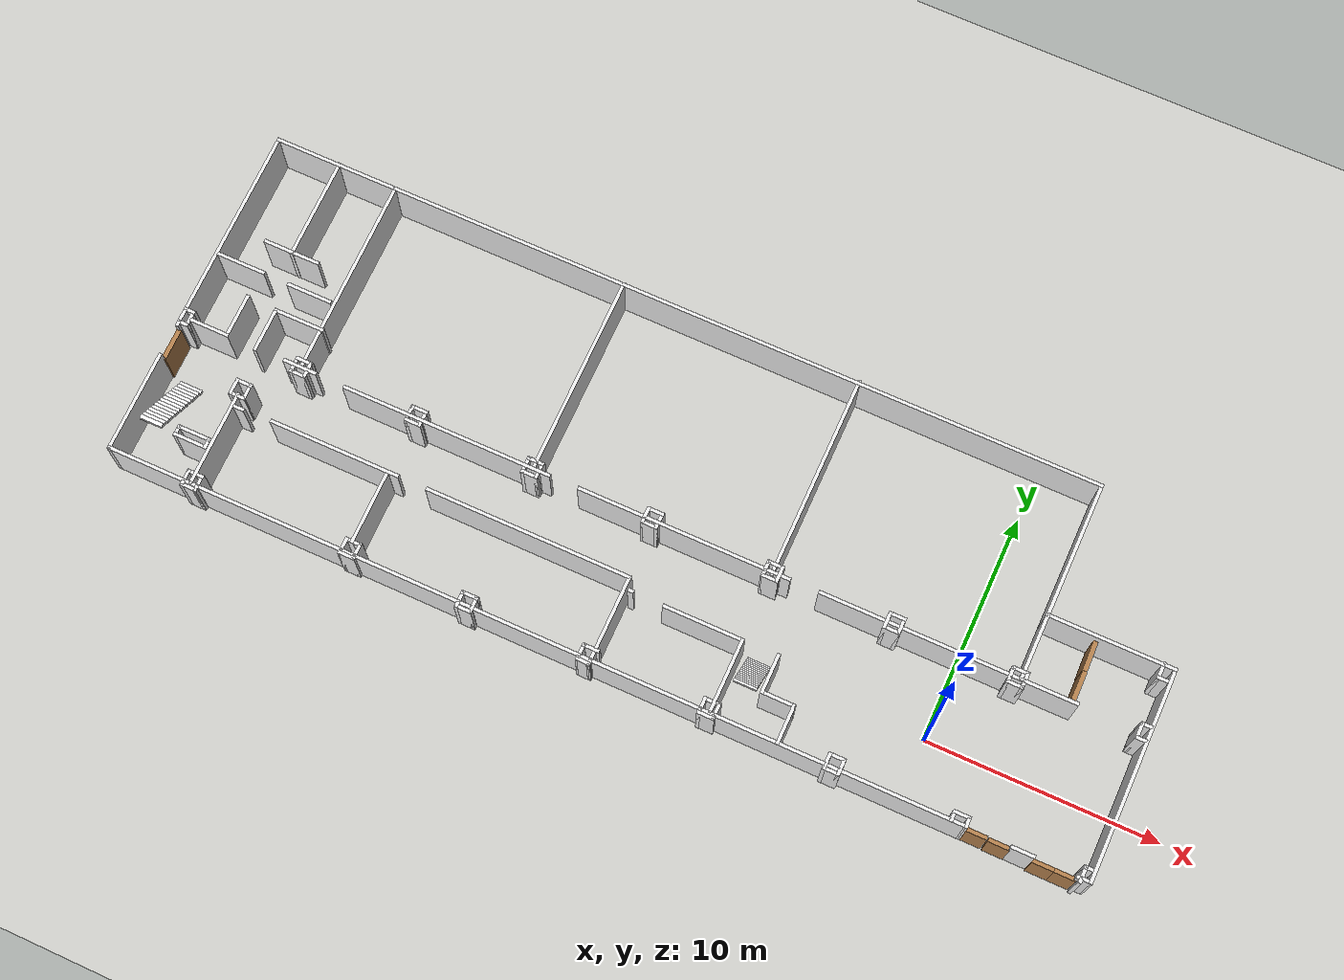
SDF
<sdf version="1.7">
 <world name="default">
  <light name="sun" type="directional">
   <pose>0 0 10 0 -0 0</pose>
   <diffuse>0.8 0.8 0.8 1</diffuse>
   <specular>0.2 0.2 0.2 1</specular>
   <attenuation>
    <range>1000</range>
    <constant>0.9</constant>
    <linear>0.01</linear>
    <quadratic>0.001</quadratic>
   </attenuation>
   <direction>-0.5 0.1 -0.9</direction>
   <spot><inner_angle>0</inner_angle><outer_angle>0</outer_angle><falloff>0</falloff></spot>
  </light>
  <model name="ground_plane">
   <static>1</static>
   <link name="link">
    <collision name="collision">
     <geometry><plane><normal>0 0 1</normal><size>100 100</size></plane></geometry>
     <surface><friction><ode><mu>100</mu><mu2>50</mu2></ode></friction></surface>
    </collision>
    <visual name="visual">
     <cast_shadows>0</cast_shadows>
     <geometry><plane><normal>0 0 1</normal><size>100 100</size></plane></geometry>
     <material>
      <script><uri>file://media/materials/scripts/gazebo.material</uri><name>Gazebo/CeilingTiled</name></script>
     </material>
    </visual>
   </link>
  </model>
  <gravity>0 0 -9.8</gravity>
  <magnetic_field>6e-06 2.3e-05 -4.2e-05</magnetic_field>
  <atmosphere type="adiabatic"/>
  <physics type="ode">
   <max_step_size>0.001</max_step_size>
   <real_time_factor>1</real_time_factor>
   <real_time_update_rate>1000</real_time_update_rate>
  </physics>
  <scene><ambient>0.6 0.6 0.6 1</ambient><background>0.7 0.7 0.7 1</background><shadows>1</shadows></scene>
  <audio><device>default</device></audio>
  <spherical_coordinates>
   <surface_model>EARTH_WGS84</surface_model>
   <latitude_deg>0</latitude_deg>
   <longitude_deg>0</longitude_deg>
   <elevation>0</elevation>
   <heading_deg>0</heading_deg>
  </spherical_coordinates>
  <model name="Peta_DC">
   <pose>-13.289 4.38092 0 0 -0 0</pose>
   <link name="Door_0">
    <collision name="Door_0_Collision">
     <geometry><box><size>0.9 0.17 2</size></box></geometry>
     <pose>0 0 1 0 -0 0</pose>
    </collision>
    <visual name="Door_0_Visual">
     <pose>0 0 1 0 -0 0</pose>
     <geometry><box><size>0.9 0.17 2</size></box></geometry>
     <material>
      <script><uri>file://media/materials/scripts/gazebo.material</uri><name>Gazebo/Wood</name></script>
     </material>
    </visual>
    <pose>16.4699 -7.39187 0 0 -0 0</pose>
   </link>
   <link name="Door_1">
    <collision name="Door_1_Collision">
     <geometry><box><size>0.9 0.17 2</size></box></geometry>
     <pose>0 0 1 0 -0 0</pose>
    </collision>
    <visual name="Door_1_Visual">
     <pose>0 0 1 0 -0 0</pose>
     <geometry><box><size>0.9 0.17 2</size></box></geometry>
     <material>
      <script><uri>file://media/materials/scripts/gazebo.material</uri><name>Gazebo/Wood</name></script>
     </material>
    </visual>
    <pose>17.4275 -7.41847 0 0 -0 0</pose>
   </link>
   <link name="Door_2">
    <collision name="Door_2_Collision">
     <geometry><box><size>0.9 0.17 2</size></box></geometry>
     <pose>0 0 1 0 -0 0</pose>
    </collision>
    <visual name="Door_2_Visual">
     <pose>0 0 1 0 -0 0</pose>
     <geometry><box><size>0.9 0.17 2</size></box></geometry>
     <material>
      <script><uri>file://media/materials/scripts/gazebo.material</uri><name>Gazebo/Wood</name></script>
     </material>
    </visual>
    <pose>19.2629 -7.47167 0 0 -0 0</pose>
   </link>
   <link name="Door_3">
    <collision name="Door_3_Collision">
     <geometry><box><size>0.9 0.17 2</size></box></geometry>
     <pose>0 0 1 0 -0 0</pose>
    </collision>
    <visual name="Door_3_Visual">
     <pose>0 0 1 0 -0 0</pose>
     <geometry><box><size>0.9 0.17 2</size></box></geometry>
     <material>
      <script><uri>file://media/materials/scripts/gazebo.material</uri><name>Gazebo/Wood</name></script>
     </material>
    </visual>
    <pose>20.1673 -7.47167 0 0 -0 0</pose>
   </link>
   <link name="Door_6">
    <collision name="Door_6_Collision">
     <geometry><box><size>1.37986 0.2 2</size></box></geometry>
     <pose>0 0 1 0 -0 0</pose>
    </collision>
    <visual name="Door_6_Visual">
     <pose>0 0 1 0 -0 0</pose>
     <geometry><box><size>1.37986 0.2 2</size></box></geometry>
     <material>
      <script><uri>file://media/materials/scripts/gazebo.material</uri><name>Gazebo/Wood</name></script>
     </material>
    </visual>
    <pose>17.9508 -0.39061 0 0 -0 1.57715</pose>
   </link>
   <link name="Door_7">
    <collision name="Door_7_Collision">
     <geometry><box><size>1.307 0.2 2</size></box></geometry>
     <pose>0 0 1 0 -0 0</pose>
    </collision>
    <visual name="Door_7_Visual">
     <pose>0 0 1 0 -0 0</pose>
     <geometry><box><size>1.307 0.2 2</size></box></geometry>
     <material>
      <script><uri>file://media/materials/scripts/gazebo.material</uri><name>Gazebo/Wood</name></script>
     </material>
    </visual>
    <pose>17.9174 0.952902 0 0 -0 1.59482</pose>
   </link>
   <link name="Door_8">
    <collision name="Door_8_Collision">
     <geometry><box><size>1.42 0.2 2</size></box></geometry>
     <pose>0 0 1 0 -0 0</pose>
    </collision>
    <visual name="Door_8_Visual">
     <pose>0 0 1 0 -0 0</pose>
     <geometry><box><size>1.42 0.2 2</size></box></geometry>
     <material>
      <script><uri>file://media/materials/scripts/gazebo.material</uri><name>Gazebo/Wood</name></script>
     </material>
    </visual>
    <pose>-21.0737 -2.32904 0 0 0 -1.5708</pose>
   </link>
   <link name="Stairs_0">
    <visual name="Stairs_0_Visual_0">
     <pose>-20.1037 -3.21304 0.083333 0 -0 0</pose>
     <geometry><box><size>1 0.178 0.166667</size></box></geometry>
     <material>
      <script><uri>file://media/materials/scripts/gazebo.material</uri><name>Gazebo/Steps</name></script>
      <ambient>1 1 1 1</ambient>
     </material>
     <meta><layer>0</layer></meta>
    </visual>
    <collision name="Stairs_0_Collision_0">
     <geometry><box><size>1 0.178 0.166667</size></box></geometry>
     <pose>-20.1037 -3.21304 0.083333 0 -0 0</pose>
    </collision>
    <visual name="Stairs_0_Visual_1">
     <pose>-20.1037 -3.39104 0.25 0 -0 0</pose>
     <geometry><box><size>1 0.178 0.166667</size></box></geometry>
     <material>
      <script><uri>file://media/materials/scripts/gazebo.material</uri><name>Gazebo/Steps</name></script>
      <ambient>1 1 1 1</ambient>
     </material>
     <meta><layer>0</layer></meta>
    </visual>
    <collision name="Stairs_0_Collision_1">
     <geometry><box><size>1 0.178 0.166667</size></box></geometry>
     <pose>-20.1037 -3.39104 0.25 0 -0 0</pose>
    </collision>
    <visual name="Stairs_0_Visual_2">
     <pose>-20.1037 -3.56904 0.416667 0 -0 0</pose>
     <geometry><box><size>1 0.178 0.166667</size></box></geometry>
     <material>
      <script><uri>file://media/materials/scripts/gazebo.material</uri><name>Gazebo/Steps</name></script>
      <ambient>1 1 1 1</ambient>
     </material>
     <meta><layer>0</layer></meta>
    </visual>
    <collision name="Stairs_0_Collision_2">
     <geometry><box><size>1 0.178 0.166667</size></box></geometry>
     <pose>-20.1037 -3.56904 0.416667 0 -0 0</pose>
    </collision>
    <visual name="Stairs_0_Visual_3">
     <pose>-20.1037 -3.74704 0.583333 0 -0 0</pose>
     <geometry><box><size>1 0.178 0.166667</size></box></geometry>
     <material>
      <script><uri>file://media/materials/scripts/gazebo.material</uri><name>Gazebo/Steps</name></script>
      <ambient>1 1 1 1</ambient>
     </material>
     <meta><layer>0</layer></meta>
    </visual>
    <collision name="Stairs_0_Collision_3">
     <geometry><box><size>1 0.178 0.166667</size></box></geometry>
     <pose>-20.1037 -3.74704 0.583333 0 -0 0</pose>
    </collision>
    <visual name="Stairs_0_Visual_4">
     <pose>-20.1037 -3.92504 0.75 0 -0 0</pose>
     <geometry><box><size>1 0.178 0.166667</size></box></geometry>
     <material>
      <script><uri>file://media/materials/scripts/gazebo.material</uri><name>Gazebo/Steps</name></script>
      <ambient>1 1 1 1</ambient>
     </material>
     <meta><layer>0</layer></meta>
    </visual>
    <collision name="Stairs_0_Collision_4">
     <geometry><box><size>1 0.178 0.166667</size></box></geometry>
     <pose>-20.1037 -3.92504 0.75 0 -0 0</pose>
    </collision>
    <visual name="Stairs_0_Visual_5">
     <pose>-20.1037 -4.10304 0.916667 0 -0 0</pose>
     <geometry><box><size>1 0.178 0.166667</size></box></geometry>
     <material>
      <script><uri>file://media/materials/scripts/gazebo.material</uri><name>Gazebo/Steps</name></script>
      <ambient>1 1 1 1</ambient>
     </material>
     <meta><layer>0</layer></meta>
    </visual>
    <collision name="Stairs_0_Collision_5">
     <geometry><box><size>1 0.178 0.166667</size></box></geometry>
     <pose>-20.1037 -4.10304 0.916667 0 -0 0</pose>
    </collision>
    <visual name="Stairs_0_Visual_6">
     <pose>-20.1037 -4.28104 1.08333 0 -0 0</pose>
     <geometry><box><size>1 0.178 0.166667</size></box></geometry>
     <material>
      <script><uri>file://media/materials/scripts/gazebo.material</uri><name>Gazebo/Steps</name></script>
      <ambient>1 1 1 1</ambient>
     </material>
     <meta><layer>0</layer></meta>
    </visual>
    <collision name="Stairs_0_Collision_6">
     <geometry><box><size>1 0.178 0.166667</size></box></geometry>
     <pose>-20.1037 -4.28104 1.08333 0 -0 0</pose>
    </collision>
    <visual name="Stairs_0_Visual_7">
     <pose>-20.1037 -4.45904 1.25 0 -0 0</pose>
     <geometry><box><size>1 0.178 0.166667</size></box></geometry>
     <material>
      <script><uri>file://media/materials/scripts/gazebo.material</uri><name>Gazebo/Steps</name></script>
      <ambient>1 1 1 1</ambient>
     </material>
     <meta><layer>0</layer></meta>
    </visual>
    <collision name="Stairs_0_Collision_7">
     <geometry><box><size>1 0.178 0.166667</size></box></geometry>
     <pose>-20.1037 -4.45904 1.25 0 -0 0</pose>
    </collision>
    <visual name="Stairs_0_Visual_8">
     <pose>-20.1037 -4.63704 1.41667 0 -0 0</pose>
     <geometry><box><size>1 0.178 0.166667</size></box></geometry>
     <material>
      <script><uri>file://media/materials/scripts/gazebo.material</uri><name>Gazebo/Steps</name></script>
      <ambient>1 1 1 1</ambient>
     </material>
     <meta><layer>0</layer></meta>
    </visual>
    <collision name="Stairs_0_Collision_8">
     <geometry><box><size>1 0.178 0.166667</size></box></geometry>
     <pose>-20.1037 -4.63704 1.41667 0 -0 0</pose>
    </collision>
    <visual name="Stairs_0_Visual_9">
     <pose>-20.1037 -4.81504 1.58333 0 -0 0</pose>
     <geometry><box><size>1 0.178 0.166667</size></box></geometry>
     <material>
      <script><uri>file://media/materials/scripts/gazebo.material</uri><name>Gazebo/Steps</name></script>
      <ambient>1 1 1 1</ambient>
     </material>
     <meta><layer>0</layer></meta>
    </visual>
    <collision name="Stairs_0_Collision_9">
     <geometry><box><size>1 0.178 0.166667</size></box></geometry>
     <pose>-20.1037 -4.81504 1.58333 0 -0 0</pose>
    </collision>
    <visual name="Stairs_0_Visual_10">
     <pose>-20.1037 -4.99304 1.75 0 -0 0</pose>
     <geometry><box><size>1 0.178 0.166667</size></box></geometry>
     <material>
      <script><uri>file://media/materials/scripts/gazebo.material</uri><name>Gazebo/Steps</name></script>
      <ambient>1 1 1 1</ambient>
     </material>
     <meta><layer>0</layer></meta>
    </visual>
    <collision name="Stairs_0_Collision_10">
     <geometry><box><size>1 0.178 0.166667</size></box></geometry>
     <pose>-20.1037 -4.99304 1.75 0 -0 0</pose>
    </collision>
    <visual name="Stairs_0_Visual_11">
     <pose>-20.1037 -5.17104 1.91667 0 -0 0</pose>
     <geometry><box><size>1 0.178 0.166667</size></box></geometry>
     <material>
      <script><uri>file://media/materials/scripts/gazebo.material</uri><name>Gazebo/Steps</name></script>
      <ambient>1 1 1 1</ambient>
     </material>
     <meta><layer>0</layer></meta>
    </visual>
    <collision name="Stairs_0_Collision_11">
     <geometry><box><size>1 0.178 0.166667</size></box></geometry>
     <pose>-20.1037 -5.17104 1.91667 0 -0 0</pose>
    </collision>
    <visual name="Stairs_0_Visual_12">
     <pose>-20.1037 -5.34904 2.08333 0 -0 0</pose>
     <geometry><box><size>1 0.178 0.166667</size></box></geometry>
     <material>
      <script><uri>file://media/materials/scripts/gazebo.material</uri><name>Gazebo/Steps</name></script>
      <ambient>1 1 1 1</ambient>
     </material>
     <meta><layer>0</layer></meta>
    </visual>
    <collision name="Stairs_0_Collision_12">
     <geometry><box><size>1 0.178 0.166667</size></box></geometry>
     <pose>-20.1037 -5.34904 2.08333 0 -0 0</pose>
    </collision>
    <visual name="Stairs_0_Visual_13">
     <pose>-20.1037 -5.52704 2.25 0 -0 0</pose>
     <geometry><box><size>1 0.178 0.166667</size></box></geometry>
     <material>
      <script><uri>file://media/materials/scripts/gazebo.material</uri><name>Gazebo/Steps</name></script>
      <ambient>1 1 1 1</ambient>
     </material>
     <meta><layer>0</layer></meta>
    </visual>
    <collision name="Stairs_0_Collision_13">
     <geometry><box><size>1 0.178 0.166667</size></box></geometry>
     <pose>-20.1037 -5.52704 2.25 0 -0 0</pose>
    </collision>
    <visual name="Stairs_0_Visual_14">
     <pose>-20.1037 -5.70504 2.41667 0 -0 0</pose>
     <geometry><box><size>1 0.178 0.166667</size></box></geometry>
     <material>
      <script><uri>file://media/materials/scripts/gazebo.material</uri><name>Gazebo/Steps</name></script>
      <ambient>1 1 1 1</ambient>
     </material>
     <meta><layer>0</layer></meta>
    </visual>
    <collision name="Stairs_0_Collision_14">
     <geometry><box><size>1 0.178 0.166667</size></box></geometry>
     <pose>-20.1037 -5.70504 2.41667 0 -0 0</pose>
    </collision>
   </link>
   <link name="Stairs_1">
    <visual name="Stairs_1_Visual_0">
     <pose>6.0533 -4.25799 0.083333 0 -0 0</pose>
     <geometry><box><size>1 0.109737 0.166667</size></box></geometry>
     <material>
      <script><uri>file://media/materials/scripts/gazebo.material</uri><name>Gazebo/Steps</name></script>
      <ambient>1 1 1 1</ambient>
     </material>
     <meta><layer>0</layer></meta>
    </visual>
    <collision name="Stairs_1_Collision_0">
     <geometry><box><size>1 0.109737 0.166667</size></box></geometry>
     <pose>6.0533 -4.25799 0.083333 0 -0 0</pose>
    </collision>
    <visual name="Stairs_1_Visual_1">
     <pose>6.0533 -4.36773 0.25 0 -0 0</pose>
     <geometry><box><size>1 0.109737 0.166667</size></box></geometry>
     <material>
      <script><uri>file://media/materials/scripts/gazebo.material</uri><name>Gazebo/Steps</name></script>
      <ambient>1 1 1 1</ambient>
     </material>
     <meta><layer>0</layer></meta>
    </visual>
    <collision name="Stairs_1_Collision_1">
     <geometry><box><size>1 0.109737 0.166667</size></box></geometry>
     <pose>6.0533 -4.36773 0.25 0 -0 0</pose>
    </collision>
    <visual name="Stairs_1_Visual_2">
     <pose>6.0533 -4.47746 0.416667 0 -0 0</pose>
     <geometry><box><size>1 0.109737 0.166667</size></box></geometry>
     <material>
      <script><uri>file://media/materials/scripts/gazebo.material</uri><name>Gazebo/Steps</name></script>
      <ambient>1 1 1 1</ambient>
     </material>
     <meta><layer>0</layer></meta>
    </visual>
    <collision name="Stairs_1_Collision_2">
     <geometry><box><size>1 0.109737 0.166667</size></box></geometry>
     <pose>6.0533 -4.47746 0.416667 0 -0 0</pose>
    </collision>
    <visual name="Stairs_1_Visual_3">
     <pose>6.0533 -4.5872 0.583333 0 -0 0</pose>
     <geometry><box><size>1 0.109737 0.166667</size></box></geometry>
     <material>
      <script><uri>file://media/materials/scripts/gazebo.material</uri><name>Gazebo/Steps</name></script>
      <ambient>1 1 1 1</ambient>
     </material>
     <meta><layer>0</layer></meta>
    </visual>
    <collision name="Stairs_1_Collision_3">
     <geometry><box><size>1 0.109737 0.166667</size></box></geometry>
     <pose>6.0533 -4.5872 0.583333 0 -0 0</pose>
    </collision>
    <visual name="Stairs_1_Visual_4">
     <pose>6.0533 -4.69694 0.75 0 -0 0</pose>
     <geometry><box><size>1 0.109737 0.166667</size></box></geometry>
     <material>
      <script><uri>file://media/materials/scripts/gazebo.material</uri><name>Gazebo/Steps</name></script>
      <ambient>1 1 1 1</ambient>
     </material>
     <meta><layer>0</layer></meta>
    </visual>
    <collision name="Stairs_1_Collision_4">
     <geometry><box><size>1 0.109737 0.166667</size></box></geometry>
     <pose>6.0533 -4.69694 0.75 0 -0 0</pose>
    </collision>
    <visual name="Stairs_1_Visual_5">
     <pose>6.0533 -4.80668 0.916667 0 -0 0</pose>
     <geometry><box><size>1 0.109737 0.166667</size></box></geometry>
     <material>
      <script><uri>file://media/materials/scripts/gazebo.material</uri><name>Gazebo/Steps</name></script>
      <ambient>1 1 1 1</ambient>
     </material>
     <meta><layer>0</layer></meta>
    </visual>
    <collision name="Stairs_1_Collision_5">
     <geometry><box><size>1 0.109737 0.166667</size></box></geometry>
     <pose>6.0533 -4.80668 0.916667 0 -0 0</pose>
    </collision>
    <visual name="Stairs_1_Visual_6">
     <pose>6.0533 -4.91641 1.08333 0 -0 0</pose>
     <geometry><box><size>1 0.109737 0.166667</size></box></geometry>
     <material>
      <script><uri>file://media/materials/scripts/gazebo.material</uri><name>Gazebo/Steps</name></script>
      <ambient>1 1 1 1</ambient>
     </material>
     <meta><layer>0</layer></meta>
    </visual>
    <collision name="Stairs_1_Collision_6">
     <geometry><box><size>1 0.109737 0.166667</size></box></geometry>
     <pose>6.0533 -4.91641 1.08333 0 -0 0</pose>
    </collision>
    <visual name="Stairs_1_Visual_7">
     <pose>6.0533 -5.02615 1.25 0 -0 0</pose>
     <geometry><box><size>1 0.109737 0.166667</size></box></geometry>
     <material>
      <script><uri>file://media/materials/scripts/gazebo.material</uri><name>Gazebo/Steps</name></script>
      <ambient>1 1 1 1</ambient>
     </material>
     <meta><layer>0</layer></meta>
    </visual>
    <collision name="Stairs_1_Collision_7">
     <geometry><box><size>1 0.109737 0.166667</size></box></geometry>
     <pose>6.0533 -5.02615 1.25 0 -0 0</pose>
    </collision>
    <visual name="Stairs_1_Visual_8">
     <pose>6.0533 -5.13589 1.41667 0 -0 0</pose>
     <geometry><box><size>1 0.109737 0.166667</size></box></geometry>
     <material>
      <script><uri>file://media/materials/scripts/gazebo.material</uri><name>Gazebo/Steps</name></script>
      <ambient>1 1 1 1</ambient>
     </material>
     <meta><layer>0</layer></meta>
    </visual>
    <collision name="Stairs_1_Collision_8">
     <geometry><box><size>1 0.109737 0.166667</size></box></geometry>
     <pose>6.0533 -5.13589 1.41667 0 -0 0</pose>
    </collision>
    <visual name="Stairs_1_Visual_9">
     <pose>6.0533 -5.24562 1.58333 0 -0 0</pose>
     <geometry><box><size>1 0.109737 0.166667</size></box></geometry>
     <material>
      <script><uri>file://media/materials/scripts/gazebo.material</uri><name>Gazebo/Steps</name></script>
      <ambient>1 1 1 1</ambient>
     </material>
     <meta><layer>0</layer></meta>
    </visual>
    <collision name="Stairs_1_Collision_9">
     <geometry><box><size>1 0.109737 0.166667</size></box></geometry>
     <pose>6.0533 -5.24562 1.58333 0 -0 0</pose>
    </collision>
    <visual name="Stairs_1_Visual_10">
     <pose>6.0533 -5.35536 1.75 0 -0 0</pose>
     <geometry><box><size>1 0.109737 0.166667</size></box></geometry>
     <material>
      <script><uri>file://media/materials/scripts/gazebo.material</uri><name>Gazebo/Steps</name></script>
      <ambient>1 1 1 1</ambient>
     </material>
     <meta><layer>0</layer></meta>
    </visual>
    <collision name="Stairs_1_Collision_10">
     <geometry><box><size>1 0.109737 0.166667</size></box></geometry>
     <pose>6.0533 -5.35536 1.75 0 -0 0</pose>
    </collision>
    <visual name="Stairs_1_Visual_11">
     <pose>6.0533 -5.4651 1.91667 0 -0 0</pose>
     <geometry><box><size>1 0.109737 0.166667</size></box></geometry>
     <material>
      <script><uri>file://media/materials/scripts/gazebo.material</uri><name>Gazebo/Steps</name></script>
      <ambient>1 1 1 1</ambient>
     </material>
     <meta><layer>0</layer></meta>
    </visual>
    <collision name="Stairs_1_Collision_11">
     <geometry><box><size>1 0.109737 0.166667</size></box></geometry>
     <pose>6.0533 -5.4651 1.91667 0 -0 0</pose>
    </collision>
    <visual name="Stairs_1_Visual_12">
     <pose>6.0533 -5.57484 2.08333 0 -0 0</pose>
     <geometry><box><size>1 0.109737 0.166667</size></box></geometry>
     <material>
      <script><uri>file://media/materials/scripts/gazebo.material</uri><name>Gazebo/Steps</name></script>
      <ambient>1 1 1 1</ambient>
     </material>
     <meta><layer>0</layer></meta>
    </visual>
    <collision name="Stairs_1_Collision_12">
     <geometry><box><size>1 0.109737 0.166667</size></box></geometry>
     <pose>6.0533 -5.57484 2.08333 0 -0 0</pose>
    </collision>
    <visual name="Stairs_1_Visual_13">
     <pose>6.0533 -5.68457 2.25 0 -0 0</pose>
     <geometry><box><size>1 0.109737 0.166667</size></box></geometry>
     <material>
      <script><uri>file://media/materials/scripts/gazebo.material</uri><name>Gazebo/Steps</name></script>
      <ambient>1 1 1 1</ambient>
     </material>
     <meta><layer>0</layer></meta>
    </visual>
    <collision name="Stairs_1_Collision_13">
     <geometry><box><size>1 0.109737 0.166667</size></box></geometry>
     <pose>6.0533 -5.68457 2.25 0 -0 0</pose>
    </collision>
    <visual name="Stairs_1_Visual_14">
     <pose>6.0533 -5.79431 2.41667 0 -0 0</pose>
     <geometry><box><size>1 0.109737 0.166667</size></box></geometry>
     <material>
      <script><uri>file://media/materials/scripts/gazebo.material</uri><name>Gazebo/Steps</name></script>
      <ambient>1 1 1 1</ambient>
     </material>
     <meta><layer>0</layer></meta>
    </visual>
    <collision name="Stairs_1_Collision_14">
     <geometry><box><size>1 0.109737 0.166667</size></box></geometry>
     <pose>6.0533 -5.79431 2.41667 0 -0 0</pose>
    </collision>
   </link>
   <link name="Wall_0">
    <collision name="Wall_0_Collision">
     <geometry><box><size>37.25 0.15 2.5</size></box></geometry>
     <pose>0 0 1.25 0 -0 0</pose>
    </collision>
    <visual name="Wall_0_Visual">
     <pose>0 0 1.25 0 -0 0</pose>
     <geometry><box><size>37.25 0.15 2.5</size></box></geometry>
     <material>
      <script><uri>file://media/materials/scripts/gazebo.material</uri><name>Gazebo/White</name></script>
      <ambient>1 1 1 1</ambient>
     </material>
     <meta><layer>0</layer></meta>
    </visual>
    <pose>-2.5644 -7.40816 0 0 -0 3.14159</pose>
   </link>
   <link name="Wall_1">
    <collision name="Wall_1_Collision">
     <geometry><box><size>4.5 0.15 2.5</size></box></geometry>
     <pose>0 0 1.25 0 -0 0</pose>
    </collision>
    <visual name="Wall_1_Visual">
     <pose>0 0 1.25 0 -0 0</pose>
     <geometry><box><size>4.5 0.15 2.5</size></box></geometry>
     <material>
      <script><uri>file://media/materials/scripts/gazebo.material</uri><name>Gazebo/White</name></script>
      <ambient>1 1 1 1</ambient>
     </material>
     <meta><layer>0</layer></meta>
    </visual>
    <pose>-21.1144 -5.23316 0 0 -0 1.5708</pose>
   </link>
   <link name="Wall_100">
    <collision name="Wall_100_Collision">
     <geometry><box><size>0.75 0.15 2.5</size></box></geometry>
     <pose>0 0 1.25 0 -0 0</pose>
    </collision>
    <visual name="Wall_100_Visual">
     <pose>0 0 1.25 0 -0 0</pose>
     <geometry><box><size>0.75 0.15 2.5</size></box></geometry>
     <material>
      <script><uri>file://media/materials/scripts/gazebo.material</uri><name>Gazebo/White</name></script>
      <ambient>1 1 1 1</ambient>
     </material>
     <meta><layer>0</layer></meta>
    </visual>
    <pose>15.6263 -1.46404 0 0 -0 3.14159</pose>
   </link>
   <link name="Wall_101">
    <collision name="Wall_101_Collision">
     <geometry><box><size>0.75 0.15 2.5</size></box></geometry>
     <pose>0 0 1.25 0 -0 0</pose>
    </collision>
    <visual name="Wall_101_Visual">
     <pose>0 0 1.25 0 -0 0</pose>
     <geometry><box><size>0.75 0.15 2.5</size></box></geometry>
     <material>
      <script><uri>file://media/materials/scripts/gazebo.material</uri><name>Gazebo/White</name></script>
      <ambient>1 1 1 1</ambient>
     </material>
     <meta><layer>0</layer></meta>
    </visual>
    <pose>15.3263 -1.16404 0 0 -0 1.5708</pose>
   </link>
   <link name="Wall_103">
    <collision name="Wall_103_Collision">
     <geometry><box><size>0.75 0.15 2.5</size></box></geometry>
     <pose>0 0 1.25 0 -0 0</pose>
    </collision>
    <visual name="Wall_103_Visual">
     <pose>0 0 1.25 0 -0 0</pose>
     <geometry><box><size>0.75 0.15 2.5</size></box></geometry>
     <material>
      <script><uri>file://media/materials/scripts/gazebo.material</uri><name>Gazebo/White</name></script>
      <ambient>1 1 1 1</ambient>
     </material>
     <meta><layer>0</layer></meta>
    </visual>
    <pose>20.6163 1.39596 0 0 -0 -1.5708</pose>
   </link>
   <link name="Wall_104">
    <collision name="Wall_104_Collision">
     <geometry><box><size>0.5 0.15 2.5</size></box></geometry>
     <pose>0 0 1.25 0 -0 0</pose>
    </collision>
    <visual name="Wall_104_Visual">
     <pose>0 0 1.25 0 -0 0</pose>
     <geometry><box><size>0.5 0.15 2.5</size></box></geometry>
     <material>
      <script><uri>file://media/materials/scripts/gazebo.material</uri><name>Gazebo/White</name></script>
      <ambient>1 1 1 1</ambient>
     </material>
     <meta><layer>0</layer></meta>
    </visual>
    <pose>20.7913 1.09596 0 0 -0 0</pose>
   </link>
   <link name="Wall_106">
    <collision name="Wall_106_Collision">
     <geometry><box><size>0.5 0.15 2.5</size></box></geometry>
     <pose>0 0 1.25 0 -0 0</pose>
    </collision>
    <visual name="Wall_106_Visual">
     <pose>0 0 1.25 0 -0 0</pose>
     <geometry><box><size>0.5 0.15 2.5</size></box></geometry>
     <material>
      <script><uri>file://media/materials/scripts/gazebo.material</uri><name>Gazebo/White</name></script>
      <ambient>1 1 1 1</ambient>
     </material>
     <meta><layer>0</layer></meta>
    </visual>
    <pose>20.8713 -0.87404 0 0 -0 3.14159</pose>
   </link>
   <link name="Wall_107">
    <collision name="Wall_107_Collision">
     <geometry><box><size>0.75 0.15 2.5</size></box></geometry>
     <pose>0 0 1.25 0 -0 0</pose>
    </collision>
    <visual name="Wall_107_Visual">
     <pose>0 0 1.25 0 -0 0</pose>
     <geometry><box><size>0.75 0.15 2.5</size></box></geometry>
     <material>
      <script><uri>file://media/materials/scripts/gazebo.material</uri><name>Gazebo/White</name></script>
      <ambient>1 1 1 1</ambient>
     </material>
     <meta><layer>0</layer></meta>
    </visual>
    <pose>20.6963 -1.17404 0 0 -0 -1.5708</pose>
   </link>
   <link name="Wall_108">
    <collision name="Wall_108_Collision">
     <geometry><box><size>0.5 0.15 2.5</size></box></geometry>
     <pose>0 0 1.25 0 -0 0</pose>
    </collision>
    <visual name="Wall_108_Visual">
     <pose>0 0 1.25 0 -0 0</pose>
     <geometry><box><size>0.5 0.15 2.5</size></box></geometry>
     <material>
      <script><uri>file://media/materials/scripts/gazebo.material</uri><name>Gazebo/White</name></script>
      <ambient>1 1 1 1</ambient>
     </material>
     <meta><layer>0</layer></meta>
    </visual>
    <pose>20.8713 -1.47404 0 0 -0 0</pose>
   </link>
   <link name="Wall_11">
    <collision name="Wall_11_Collision">
     <geometry><box><size>0.66993 0.15 2.5</size></box></geometry>
     <pose>0 0 1.25 0 -0 0</pose>
    </collision>
    <visual name="Wall_11_Visual">
     <pose>0 0 1.25 0 -0 0</pose>
     <geometry><box><size>0.66993 0.15 2.5</size></box></geometry>
     <material>
      <script><uri>file://media/materials/scripts/gazebo.material</uri><name>Gazebo/White</name></script>
      <ambient>1 1 1 1</ambient>
     </material>
     <meta><layer>0</layer></meta>
    </visual>
    <pose>20.8528 -7.43908 0 0 -0 0.023062</pose>
   </link>
   <link name="Wall_110">
    <collision name="Wall_110_Collision">
     <geometry><box><size>0.5 0.15 2.5</size></box></geometry>
     <pose>0 0 1.25 0 -0 0</pose>
    </collision>
    <visual name="Wall_110_Visual">
     <pose>0 0 1.25 0 -0 0</pose>
     <geometry><box><size>0.5 0.15 2.5</size></box></geometry>
     <material>
      <script><uri>file://media/materials/scripts/gazebo.material</uri><name>Gazebo/White</name></script>
      <ambient>1 1 1 1</ambient>
     </material>
     <meta><layer>0</layer></meta>
    </visual>
    <pose>20.9013 -6.97404 0 0 -0 3.14159</pose>
   </link>
   <link name="Wall_111">
    <collision name="Wall_111_Collision">
     <geometry><box><size>0.75 0.15 2.5</size></box></geometry>
     <pose>0 0 1.25 0 -0 0</pose>
    </collision>
    <visual name="Wall_111_Visual">
     <pose>0 0 1.25 0 -0 0</pose>
     <geometry><box><size>0.75 0.15 2.5</size></box></geometry>
     <material>
      <script><uri>file://media/materials/scripts/gazebo.material</uri><name>Gazebo/White</name></script>
      <ambient>1 1 1 1</ambient>
     </material>
     <meta><layer>0</layer></meta>
    </visual>
    <pose>20.7263 -7.27404 0 0 -0 -1.5708</pose>
   </link>
   <link name="Wall_113">
    <collision name="Wall_113_Collision">
     <geometry><box><size>0.5 0.15 2.5</size></box></geometry>
     <pose>0 0 1.25 0 -0 0</pose>
    </collision>
    <visual name="Wall_113_Visual">
     <pose>0 0 1.25 0 -0 0</pose>
     <geometry><box><size>0.5 0.15 2.5</size></box></geometry>
     <material>
      <script><uri>file://media/materials/scripts/gazebo.material</uri><name>Gazebo/White</name></script>
      <ambient>1 1 1 1</ambient>
     </material>
     <meta><layer>0</layer></meta>
    </visual>
    <pose>15.3763 -7.22904 0 0 -0 1.5708</pose>
   </link>
   <link name="Wall_114">
    <collision name="Wall_114_Collision">
     <geometry><box><size>0.75 0.15 2.5</size></box></geometry>
     <pose>0 0 1.25 0 -0 0</pose>
    </collision>
    <visual name="Wall_114_Visual">
     <pose>0 0 1.25 0 -0 0</pose>
     <geometry><box><size>0.75 0.15 2.5</size></box></geometry>
     <material>
      <script><uri>file://media/materials/scripts/gazebo.material</uri><name>Gazebo/White</name></script>
      <ambient>1 1 1 1</ambient>
     </material>
     <meta><layer>0</layer></meta>
    </visual>
    <pose>15.6763 -7.05404 0 0 -0 0</pose>
   </link>
   <link name="Wall_115">
    <collision name="Wall_115_Collision">
     <geometry><box><size>0.504245 0.15 2.5</size></box></geometry>
     <pose>0 0 1.25 0 -0 0</pose>
    </collision>
    <visual name="Wall_115_Visual">
     <pose>0 0 1.25 0 -0 0</pose>
     <geometry><box><size>0.504245 0.15 2.5</size></box></geometry>
     <material>
      <script><uri>file://media/materials/scripts/gazebo.material</uri><name>Gazebo/White</name></script>
      <ambient>1 1 1 1</ambient>
     </material>
     <meta><layer>0</layer></meta>
    </visual>
    <pose>15.9809 -7.2311 0 0 -0 -1.54451</pose>
   </link>
   <link name="Wall_117">
    <collision name="Wall_117_Collision">
     <geometry><box><size>0.75 0.15 2.5</size></box></geometry>
     <pose>0 0 1.25 0 -0 0</pose>
    </collision>
    <visual name="Wall_117_Visual">
     <pose>0 0 1.25 0 -0 0</pose>
     <geometry><box><size>0.75 0.15 2.5</size></box></geometry>
     <material>
      <script><uri>file://media/materials/scripts/gazebo.material</uri><name>Gazebo/White</name></script>
      <ambient>1 1 1 1</ambient>
     </material>
     <meta><layer>0</layer></meta>
    </visual>
    <pose>10.1363 -7.26404 0 0 -0 1.5708</pose>
   </link>
   <link name="Wall_118">
    <collision name="Wall_118_Collision">
     <geometry><box><size>0.75 0.15 2.5</size></box></geometry>
     <pose>0 0 1.25 0 -0 0</pose>
    </collision>
    <visual name="Wall_118_Visual">
     <pose>0 0 1.25 0 -0 0</pose>
     <geometry><box><size>0.75 0.15 2.5</size></box></geometry>
     <material>
      <script><uri>file://media/materials/scripts/gazebo.material</uri><name>Gazebo/White</name></script>
      <ambient>1 1 1 1</ambient>
     </material>
     <meta><layer>0</layer></meta>
    </visual>
    <pose>10.4363 -6.96404 0 0 -0 0</pose>
   </link>
   <link name="Wall_119">
    <collision name="Wall_119_Collision">
     <geometry><box><size>0.75 0.15 2.5</size></box></geometry>
     <pose>0 0 1.25 0 -0 0</pose>
    </collision>
    <visual name="Wall_119_Visual">
     <pose>0 0 1.25 0 -0 0</pose>
     <geometry><box><size>0.75 0.15 2.5</size></box></geometry>
     <material>
      <script><uri>file://media/materials/scripts/gazebo.material</uri><name>Gazebo/White</name></script>
      <ambient>1 1 1 1</ambient>
     </material>
     <meta><layer>0</layer></meta>
    </visual>
    <pose>10.7363 -7.26404 0 0 -0 -1.5708</pose>
   </link>
   <link name="Wall_120">
    <collision name="Wall_120_Collision">
     <geometry><box><size>0.75 0.15 2.5</size></box></geometry>
     <pose>0 0 1.25 0 -0 0</pose>
    </collision>
    <visual name="Wall_120_Visual">
     <pose>0 0 1.25 0 -0 0</pose>
     <geometry><box><size>0.75 0.15 2.5</size></box></geometry>
     <material>
      <script><uri>file://media/materials/scripts/gazebo.material</uri><name>Gazebo/White</name></script>
      <ambient>1 1 1 1</ambient>
     </material>
     <meta><layer>0</layer></meta>
    </visual>
    <pose>10.4363 -7.56404 0 0 -0 3.14159</pose>
   </link>
   <link name="Wall_122">
    <collision name="Wall_122_Collision">
     <geometry><box><size>0.75 0.15 2.5</size></box></geometry>
     <pose>0 0 1.25 0 -0 0</pose>
    </collision>
    <visual name="Wall_122_Visual">
     <pose>0 0 1.25 0 -0 0</pose>
     <geometry><box><size>0.75 0.15 2.5</size></box></geometry>
     <material>
      <script><uri>file://media/materials/scripts/gazebo.material</uri><name>Gazebo/White</name></script>
      <ambient>1 1 1 1</ambient>
     </material>
     <meta><layer>0</layer></meta>
    </visual>
    <pose>5.15629 -6.95404 0 0 -0 0</pose>
   </link>
   <link name="Wall_123">
    <collision name="Wall_123_Collision">
     <geometry><box><size>0.75 0.15 2.5</size></box></geometry>
     <pose>0 0 1.25 0 -0 0</pose>
    </collision>
    <visual name="Wall_123_Visual">
     <pose>0 0 1.25 0 -0 0</pose>
     <geometry><box><size>0.75 0.15 2.5</size></box></geometry>
     <material>
      <script><uri>file://media/materials/scripts/gazebo.material</uri><name>Gazebo/White</name></script>
      <ambient>1 1 1 1</ambient>
     </material>
     <meta><layer>0</layer></meta>
    </visual>
    <pose>5.45629 -7.25404 0 0 -0 -1.5708</pose>
   </link>
   <link name="Wall_124">
    <collision name="Wall_124_Collision">
     <geometry><box><size>0.75 0.15 2.5</size></box></geometry>
     <pose>0 0 1.25 0 -0 0</pose>
    </collision>
    <visual name="Wall_124_Visual">
     <pose>0 0 1.25 0 -0 0</pose>
     <geometry><box><size>0.75 0.15 2.5</size></box></geometry>
     <material>
      <script><uri>file://media/materials/scripts/gazebo.material</uri><name>Gazebo/White</name></script>
      <ambient>1 1 1 1</ambient>
     </material>
     <meta><layer>0</layer></meta>
    </visual>
    <pose>5.15629 -7.55404 0 0 -0 3.14159</pose>
   </link>
   <link name="Wall_125">
    <collision name="Wall_125_Collision">
     <geometry><box><size>0.75 0.15 2.5</size></box></geometry>
     <pose>0 0 1.25 0 -0 0</pose>
    </collision>
    <visual name="Wall_125_Visual">
     <pose>0 0 1.25 0 -0 0</pose>
     <geometry><box><size>0.75 0.15 2.5</size></box></geometry>
     <material>
      <script><uri>file://media/materials/scripts/gazebo.material</uri><name>Gazebo/White</name></script>
      <ambient>1 1 1 1</ambient>
     </material>
     <meta><layer>0</layer></meta>
    </visual>
    <pose>4.85629 -7.25404 0 0 -0 1.5708</pose>
   </link>
   <link name="Wall_127">
    <collision name="Wall_127_Collision">
     <geometry><box><size>0.75 0.15 2.5</size></box></geometry>
     <pose>0 0 1.25 0 -0 0</pose>
    </collision>
    <visual name="Wall_127_Visual">
     <pose>0 0 1.25 0 -0 0</pose>
     <geometry><box><size>0.75 0.15 2.5</size></box></geometry>
     <material>
      <script><uri>file://media/materials/scripts/gazebo.material</uri><name>Gazebo/White</name></script>
      <ambient>1 1 1 1</ambient>
     </material>
     <meta><layer>0</layer></meta>
    </visual>
    <pose>-5.57371 -7.28404 0 0 -0 1.5708</pose>
   </link>
   <link name="Wall_128">
    <collision name="Wall_128_Collision">
     <geometry><box><size>0.75 0.15 2.5</size></box></geometry>
     <pose>0 0 1.25 0 -0 0</pose>
    </collision>
    <visual name="Wall_128_Visual">
     <pose>0 0 1.25 0 -0 0</pose>
     <geometry><box><size>0.75 0.15 2.5</size></box></geometry>
     <material>
      <script><uri>file://media/materials/scripts/gazebo.material</uri><name>Gazebo/White</name></script>
      <ambient>1 1 1 1</ambient>
     </material>
     <meta><layer>0</layer></meta>
    </visual>
    <pose>-5.27371 -6.98404 0 0 -0 0</pose>
   </link>
   <link name="Wall_129">
    <collision name="Wall_129_Collision">
     <geometry><box><size>0.75 0.15 2.5</size></box></geometry>
     <pose>0 0 1.25 0 -0 0</pose>
    </collision>
    <visual name="Wall_129_Visual">
     <pose>0 0 1.25 0 -0 0</pose>
     <geometry><box><size>0.75 0.15 2.5</size></box></geometry>
     <material>
      <script><uri>file://media/materials/scripts/gazebo.material</uri><name>Gazebo/White</name></script>
      <ambient>1 1 1 1</ambient>
     </material>
     <meta><layer>0</layer></meta>
    </visual>
    <pose>-4.97371 -7.28404 0 0 -0 -1.5708</pose>
   </link>
   <link name="Wall_13">
    <collision name="Wall_13_Collision">
     <geometry><box><size>3 0.15 2.5</size></box></geometry>
     <pose>0 0 1.25 0 -0 0</pose>
    </collision>
    <visual name="Wall_13_Visual">
     <pose>0 0 1.25 0 -0 0</pose>
     <geometry><box><size>3 0.15 2.5</size></box></geometry>
     <material>
      <script><uri>file://media/materials/scripts/gazebo.material</uri><name>Gazebo/White</name></script>
      <ambient>1 1 1 1</ambient>
     </material>
     <meta><layer>0</layer></meta>
    </visual>
    <pose>15.7627 0.241917 0 0 -0 -1.5708</pose>
   </link>
   <link name="Wall_130">
    <collision name="Wall_130_Collision">
     <geometry><box><size>0.75 0.15 2.5</size></box></geometry>
     <pose>0 0 1.25 0 -0 0</pose>
    </collision>
    <visual name="Wall_130_Visual">
     <pose>0 0 1.25 0 -0 0</pose>
     <geometry><box><size>0.75 0.15 2.5</size></box></geometry>
     <material>
      <script><uri>file://media/materials/scripts/gazebo.material</uri><name>Gazebo/White</name></script>
      <ambient>1 1 1 1</ambient>
     </material>
     <meta><layer>0</layer></meta>
    </visual>
    <pose>-5.27371 -7.58404 0 0 -0 3.14159</pose>
   </link>
   <link name="Wall_132">
    <collision name="Wall_132_Collision">
     <geometry><box><size>0.75 0.15 2.5</size></box></geometry>
     <pose>0 0 1.25 0 -0 0</pose>
    </collision>
    <visual name="Wall_132_Visual">
     <pose>0 0 1.25 0 -0 0</pose>
     <geometry><box><size>0.75 0.15 2.5</size></box></geometry>
     <material>
      <script><uri>file://media/materials/scripts/gazebo.material</uri><name>Gazebo/White</name></script>
      <ambient>1 1 1 1</ambient>
     </material>
     <meta><layer>0</layer></meta>
    </visual>
    <pose>-0.033709 -6.95404 0 0 -0 0</pose>
   </link>
   <link name="Wall_134">
    <collision name="Wall_134_Collision">
     <geometry><box><size>0.75 0.15 2.5</size></box></geometry>
     <pose>0 0 1.25 0 -0 0</pose>
    </collision>
    <visual name="Wall_134_Visual">
     <pose>0 0 1.25 0 -0 0</pose>
     <geometry><box><size>0.75 0.15 2.5</size></box></geometry>
     <material>
      <script><uri>file://media/materials/scripts/gazebo.material</uri><name>Gazebo/White</name></script>
      <ambient>1 1 1 1</ambient>
     </material>
     <meta><layer>0</layer></meta>
    </visual>
    <pose>-0.333709 -7.25404 0 0 -0 -1.5708</pose>
   </link>
   <link name="Wall_135">
    <collision name="Wall_135_Collision">
     <geometry><box><size>0.640084 0.15 2.5</size></box></geometry>
     <pose>0 0 1.25 0 -0 0</pose>
    </collision>
    <visual name="Wall_135_Visual">
     <pose>0 0 1.25 0 -0 0</pose>
     <geometry><box><size>0.640084 0.15 2.5</size></box></geometry>
     <material>
      <script><uri>file://media/materials/scripts/gazebo.material</uri><name>Gazebo/White</name></script>
      <ambient>1 1 1 1</ambient>
     </material>
     <meta><layer>0</layer></meta>
    </visual>
    <pose>-0.088815 -7.56254 0 0 -0 -0.034705</pose>
   </link>
   <link name="Wall_137">
    <collision name="Wall_137_Collision">
     <geometry><box><size>3.25 0.15 2.5</size></box></geometry>
     <pose>0 0 1.25 0 -0 0</pose>
    </collision>
    <visual name="Wall_137_Visual">
     <pose>0 0 1.25 0 -0 0</pose>
     <geometry><box><size>3.25 0.15 2.5</size></box></geometry>
     <material>
      <script><uri>file://media/materials/scripts/gazebo.material</uri><name>Gazebo/White</name></script>
      <ambient>1 1 1 1</ambient>
     </material>
     <meta><layer>0</layer></meta>
    </visual>
    <pose>-10.4737 -5.36404 0 0 -0 -1.5708</pose>
   </link>
   <link name="Wall_138">
    <collision name="Wall_138_Collision">
     <geometry><box><size>0.5 0.15 2.5</size></box></geometry>
     <pose>0 0 1.25 0 -0 0</pose>
    </collision>
    <visual name="Wall_138_Visual">
     <pose>0 0 1.25 0 -0 0</pose>
     <geometry><box><size>0.5 0.15 2.5</size></box></geometry>
     <material>
      <script><uri>file://media/materials/scripts/gazebo.material</uri><name>Gazebo/White</name></script>
      <ambient>1 1 1 1</ambient>
     </material>
     <meta><layer>0</layer></meta>
    </visual>
    <pose>-10.2987 -6.91404 0 0 -0 0</pose>
   </link>
   <link name="Wall_139">
    <collision name="Wall_139_Collision">
     <geometry><box><size>0.75 0.15 2.5</size></box></geometry>
     <pose>0 0 1.25 0 -0 0</pose>
    </collision>
    <visual name="Wall_139_Visual">
     <pose>0 0 1.25 0 -0 0</pose>
     <geometry><box><size>0.75 0.15 2.5</size></box></geometry>
     <material>
      <script><uri>file://media/materials/scripts/gazebo.material</uri><name>Gazebo/White</name></script>
      <ambient>1 1 1 1</ambient>
     </material>
     <meta><layer>0</layer></meta>
    </visual>
    <pose>-10.1237 -7.21404 0 0 -0 -1.5708</pose>
   </link>
   <link name="Wall_14">
    <collision name="Wall_14_Collision">
     <geometry><box><size>2.5 0.15 2.5</size></box></geometry>
     <pose>0 0 1.25 0 -0 0</pose>
    </collision>
    <visual name="Wall_14_Visual">
     <pose>0 0 1.25 0 -0 0</pose>
     <geometry><box><size>2.5 0.15 2.5</size></box></geometry>
     <material>
      <script><uri>file://media/materials/scripts/gazebo.material</uri><name>Gazebo/White</name></script>
      <ambient>1 1 1 1</ambient>
     </material>
     <meta><layer>0</layer></meta>
    </visual>
    <pose>16.9377 -1.18308 0 0 -0 0</pose>
   </link>
   <link name="Wall_140">
    <collision name="Wall_140_Collision">
     <geometry><box><size>0.75 0.15 2.5</size></box></geometry>
     <pose>0 0 1.25 0 -0 0</pose>
    </collision>
    <visual name="Wall_140_Visual">
     <pose>0 0 1.25 0 -0 0</pose>
     <geometry><box><size>0.75 0.15 2.5</size></box></geometry>
     <material>
      <script><uri>file://media/materials/scripts/gazebo.material</uri><name>Gazebo/White</name></script>
      <ambient>1 1 1 1</ambient>
     </material>
     <meta><layer>0</layer></meta>
    </visual>
    <pose>-10.4237 -7.51404 0 0 -0 3.14159</pose>
   </link>
   <link name="Wall_141">
    <collision name="Wall_141_Collision">
     <geometry><box><size>0.75 0.15 2.5</size></box></geometry>
     <pose>0 0 1.25 0 -0 0</pose>
    </collision>
    <visual name="Wall_141_Visual">
     <pose>0 0 1.25 0 -0 0</pose>
     <geometry><box><size>0.75 0.15 2.5</size></box></geometry>
     <material>
      <script><uri>file://media/materials/scripts/gazebo.material</uri><name>Gazebo/White</name></script>
      <ambient>1 1 1 1</ambient>
     </material>
     <meta><layer>0</layer></meta>
    </visual>
    <pose>-10.7237 -7.21404 0 0 -0 1.5708</pose>
   </link>
   <link name="Wall_142">
    <collision name="Wall_142_Collision">
     <geometry><box><size>0.4 0.15 2.5</size></box></geometry>
     <pose>0 0 1.25 0 -0 0</pose>
    </collision>
    <visual name="Wall_142_Visual">
     <pose>0 0 1.25 0 -0 0</pose>
     <geometry><box><size>0.4 0.15 2.5</size></box></geometry>
     <material>
      <script><uri>file://media/materials/scripts/gazebo.material</uri><name>Gazebo/White</name></script>
      <ambient>1 1 1 1</ambient>
     </material>
     <meta><layer>0</layer></meta>
    </visual>
    <pose>-10.5987 -6.91404 0 0 -0 0</pose>
   </link>
   <link name="Wall_144">
    <collision name="Wall_144_Collision">
     <geometry><box><size>0.75 0.15 2.5</size></box></geometry>
     <pose>0 0 1.25 0 -0 0</pose>
    </collision>
    <visual name="Wall_144_Visual">
     <pose>0 0 1.25 0 -0 0</pose>
     <geometry><box><size>0.75 0.15 2.5</size></box></geometry>
     <material>
      <script><uri>file://media/materials/scripts/gazebo.material</uri><name>Gazebo/White</name></script>
      <ambient>1 1 1 1</ambient>
     </material>
     <meta><layer>0</layer></meta>
    </visual>
    <pose>-17.4437 -6.97404 0 0 -0 0</pose>
   </link>
   <link name="Wall_145">
    <collision name="Wall_145_Collision">
     <geometry><box><size>0.75 0.15 2.5</size></box></geometry>
     <pose>0 0 1.25 0 -0 0</pose>
    </collision>
    <visual name="Wall_145_Visual">
     <pose>0 0 1.25 0 -0 0</pose>
     <geometry><box><size>0.75 0.15 2.5</size></box></geometry>
     <material>
      <script><uri>file://media/materials/scripts/gazebo.material</uri><name>Gazebo/White</name></script>
      <ambient>1 1 1 1</ambient>
     </material>
     <meta><layer>0</layer></meta>
    </visual>
    <pose>-17.1437 -7.27404 0 0 -0 -1.5708</pose>
   </link>
   <link name="Wall_146">
    <collision name="Wall_146_Collision">
     <geometry><box><size>0.75 0.15 2.5</size></box></geometry>
     <pose>0 0 1.25 0 -0 0</pose>
    </collision>
    <visual name="Wall_146_Visual">
     <pose>0 0 1.25 0 -0 0</pose>
     <geometry><box><size>0.75 0.15 2.5</size></box></geometry>
     <material>
      <script><uri>file://media/materials/scripts/gazebo.material</uri><name>Gazebo/White</name></script>
      <ambient>1 1 1 1</ambient>
     </material>
     <meta><layer>0</layer></meta>
    </visual>
    <pose>-17.4437 -7.57404 0 0 -0 3.14159</pose>
   </link>
   <link name="Wall_147">
    <collision name="Wall_147_Collision">
     <geometry><box><size>0.75 0.15 2.5</size></box></geometry>
     <pose>0 0 1.25 0 -0 0</pose>
    </collision>
    <visual name="Wall_147_Visual">
     <pose>0 0 1.25 0 -0 0</pose>
     <geometry><box><size>0.75 0.15 2.5</size></box></geometry>
     <material>
      <script><uri>file://media/materials/scripts/gazebo.material</uri><name>Gazebo/White</name></script>
      <ambient>1 1 1 1</ambient>
     </material>
     <meta><layer>0</layer></meta>
    </visual>
    <pose>-17.7437 -7.27404 0 0 -0 1.5708</pose>
   </link>
   <link name="Wall_149">
    <collision name="Wall_149_Collision">
     <geometry><box><size>1.5 0.15 2.5</size></box></geometry>
     <pose>0 0 1.25 0 -0 0</pose>
    </collision>
    <visual name="Wall_149_Visual">
     <pose>0 0 1.25 0 -0 0</pose>
     <geometry><box><size>1.5 0.15 2.5</size></box></geometry>
     <material>
      <script><uri>file://media/materials/scripts/gazebo.material</uri><name>Gazebo/White</name></script>
      <ambient>1 1 1 1</ambient>
     </material>
     <meta><layer>0</layer></meta>
    </visual>
    <pose>-18.2887 -5.46404 0 0 -0 0</pose>
   </link>
   <link name="Wall_15">
    <collision name="Wall_15_Collision">
     <geometry><box><size>11 0.15 2.5</size></box></geometry>
     <pose>0 0 1.25 0 -0 0</pose>
    </collision>
    <visual name="Wall_15_Visual">
     <pose>0 0 1.25 0 -0 0</pose>
     <geometry><box><size>11 0.15 2.5</size></box></geometry>
     <material>
      <script><uri>file://media/materials/scripts/gazebo.material</uri><name>Gazebo/White</name></script>
      <ambient>1 1 1 1</ambient>
     </material>
     <meta><layer>0</layer></meta>
    </visual>
    <pose>12.6877 -1.18308 0 0 -0 3.14159</pose>
   </link>
   <link name="Wall_150">
    <collision name="Wall_150_Collision">
     <geometry><box><size>0.5 0.15 2.5</size></box></geometry>
     <pose>0 0 1.25 0 -0 0</pose>
    </collision>
    <visual name="Wall_150_Visual">
     <pose>0 0 1.25 0 -0 0</pose>
     <geometry><box><size>0.5 0.15 2.5</size></box></geometry>
     <material>
      <script><uri>file://media/materials/scripts/gazebo.material</uri><name>Gazebo/White</name></script>
      <ambient>1 1 1 1</ambient>
     </material>
     <meta><layer>0</layer></meta>
    </visual>
    <pose>-17.6137 -5.63904 0 0 -0 -1.5708</pose>
   </link>
   <link name="Wall_151">
    <collision name="Wall_151_Collision">
     <geometry><box><size>1.5 0.15 2.5</size></box></geometry>
     <pose>0 0 1.25 0 -0 0</pose>
    </collision>
    <visual name="Wall_151_Visual">
     <pose>0 0 1.25 0 -0 0</pose>
     <geometry><box><size>1.5 0.15 2.5</size></box></geometry>
     <material>
      <script><uri>file://media/materials/scripts/gazebo.material</uri><name>Gazebo/White</name></script>
      <ambient>1 1 1 1</ambient>
     </material>
     <meta><layer>0</layer></meta>
    </visual>
    <pose>-18.2887 -5.81404 0 0 -0 3.14159</pose>
   </link>
   <link name="Wall_152">
    <collision name="Wall_152_Collision">
     <geometry><box><size>0.5 0.15 2.5</size></box></geometry>
     <pose>0 0 1.25 0 -0 0</pose>
    </collision>
    <visual name="Wall_152_Visual">
     <pose>0 0 1.25 0 -0 0</pose>
     <geometry><box><size>0.5 0.15 2.5</size></box></geometry>
     <material>
      <script><uri>file://media/materials/scripts/gazebo.material</uri><name>Gazebo/White</name></script>
      <ambient>1 1 1 1</ambient>
     </material>
     <meta><layer>0</layer></meta>
    </visual>
    <pose>-18.9637 -5.63904 0 0 -0 1.5708</pose>
   </link>
   <link name="Wall_154">
    <collision name="Wall_154_Collision">
     <geometry><box><size>1.75 0.15 2.5</size></box></geometry>
     <pose>0 0 1.25 0 -0 0</pose>
    </collision>
    <visual name="Wall_154_Visual">
     <pose>0 0 1.25 0 -0 0</pose>
     <geometry><box><size>1.75 0.15 2.5</size></box></geometry>
     <material>
      <script><uri>file://media/materials/scripts/gazebo.material</uri><name>Gazebo/White</name></script>
      <ambient>1 1 1 1</ambient>
     </material>
     <meta><layer>0</layer></meta>
    </visual>
    <pose>6.77039 -5.00412 0 0 -0 -1.5708</pose>
   </link>
   <link name="Wall_155">
    <collision name="Wall_155_Collision">
     <geometry><box><size>1.5 0.15 2.5</size></box></geometry>
     <pose>0 0 1.25 0 -0 0</pose>
    </collision>
    <visual name="Wall_155_Visual">
     <pose>0 0 1.25 0 -0 0</pose>
     <geometry><box><size>1.5 0.15 2.5</size></box></geometry>
     <material>
      <script><uri>file://media/materials/scripts/gazebo.material</uri><name>Gazebo/White</name></script>
      <ambient>1 1 1 1</ambient>
     </material>
     <meta><layer>0</layer></meta>
    </visual>
    <pose>7.4454 -5.80412 0 0 -0 0</pose>
   </link>
   <link name="Wall_156">
    <collision name="Wall_156_Collision">
     <geometry><box><size>1.75 0.15 2.5</size></box></geometry>
     <pose>0 0 1.25 0 -0 0</pose>
    </collision>
    <visual name="Wall_156_Visual">
     <pose>0 0 1.25 0 -0 0</pose>
     <geometry><box><size>1.75 0.15 2.5</size></box></geometry>
     <material>
      <script><uri>file://media/materials/scripts/gazebo.material</uri><name>Gazebo/White</name></script>
      <ambient>1 1 1 1</ambient>
     </material>
     <meta><layer>0</layer></meta>
    </visual>
    <pose>8.12039 -6.60412 0 0 -0 -1.5708</pose>
   </link>
   <link name="Wall_17">
    <collision name="Wall_17_Collision">
     <geometry><box><size>9.25 0.15 2.5</size></box></geometry>
     <pose>0 0 1.25 0 -0 0</pose>
    </collision>
    <visual name="Wall_17_Visual">
     <pose>0 0 1.25 0 -0 0</pose>
     <geometry><box><size>9.25 0.15 2.5</size></box></geometry>
     <material>
      <script><uri>file://media/materials/scripts/gazebo.material</uri><name>Gazebo/White</name></script>
      <ambient>1 1 1 1</ambient>
     </material>
     <meta><layer>0</layer></meta>
    </visual>
    <pose>1.35959 -1.19403 0 0 -0 3.14159</pose>
   </link>
   <link name="Wall_19">
    <collision name="Wall_19_Collision">
     <geometry><box><size>9.25 0.15 2.5</size></box></geometry>
     <pose>0 0 1.25 0 -0 0</pose>
    </collision>
    <visual name="Wall_19_Visual">
     <pose>0 0 1.25 0 -0 0</pose>
     <geometry><box><size>9.25 0.15 2.5</size></box></geometry>
     <material>
      <script><uri>file://media/materials/scripts/gazebo.material</uri><name>Gazebo/White</name></script>
      <ambient>1 1 1 1</ambient>
     </material>
     <meta><layer>0</layer></meta>
    </visual>
    <pose>-9.09929 -1.20243 0 0 -0 3.14159</pose>
   </link>
   <link name="Wall_21">
    <collision name="Wall_21_Collision">
     <geometry><box><size>1.5 0.15 2.5</size></box></geometry>
     <pose>0 0 1.25 0 -0 0</pose>
    </collision>
    <visual name="Wall_21_Visual">
     <pose>0 0 1.25 0 -0 0</pose>
     <geometry><box><size>1.5 0.15 2.5</size></box></geometry>
     <material>
      <script><uri>file://media/materials/scripts/gazebo.material</uri><name>Gazebo/White</name></script>
      <ambient>1 1 1 1</ambient>
     </material>
     <meta><layer>0</layer></meta>
    </visual>
    <pose>-15.6998 -1.16743 0 0 -0 3.14159</pose>
   </link>
   <link name="Wall_23">
    <collision name="Wall_23_Collision">
     <geometry><box><size>8.75 0.15 2.5</size></box></geometry>
     <pose>0 0 1.25 0 -0 0</pose>
    </collision>
    <visual name="Wall_23_Visual">
     <pose>0 0 1.25 0 -0 0</pose>
     <geometry><box><size>8.75 0.15 2.5</size></box></geometry>
     <material>
      <script><uri>file://media/materials/scripts/gazebo.material</uri><name>Gazebo/White</name></script>
      <ambient>1 1 1 1</ambient>
     </material>
     <meta><layer>0</layer></meta>
    </visual>
    <pose>-15.6632 3.20424 0 0 -0 -1.5708</pose>
   </link>
   <link name="Wall_25">
    <collision name="Wall_25_Collision">
     <geometry><box><size>0.75 0.15 2.5</size></box></geometry>
     <pose>0 0 1.25 0 -0 0</pose>
    </collision>
    <visual name="Wall_25_Visual">
     <pose>0 0 1.25 0 -0 0</pose>
     <geometry><box><size>0.75 0.15 2.5</size></box></geometry>
     <material>
      <script><uri>file://media/materials/scripts/gazebo.material</uri><name>Gazebo/White</name></script>
      <ambient>1 1 1 1</ambient>
     </material>
     <meta><layer>0</layer></meta>
    </visual>
    <pose>-15.6558 -0.874824 0 0 -0 0</pose>
   </link>
   <link name="Wall_28">
    <collision name="Wall_28_Collision">
     <geometry><box><size>0.75 0.15 2.5</size></box></geometry>
     <pose>0 0 1.25 0 -0 0</pose>
    </collision>
    <visual name="Wall_28_Visual">
     <pose>0 0 1.25 0 -0 0</pose>
     <geometry><box><size>0.75 0.15 2.5</size></box></geometry>
     <material>
      <script><uri>file://media/materials/scripts/gazebo.material</uri><name>Gazebo/White</name></script>
      <ambient>1 1 1 1</ambient>
     </material>
     <meta><layer>0</layer></meta>
    </visual>
    <pose>-15.3558 -1.17482 0 0 -0 -1.5708</pose>
   </link>
   <link name="Wall_29">
    <collision name="Wall_29_Collision">
     <geometry><box><size>0.75 0.15 2.5</size></box></geometry>
     <pose>0 0 1.25 0 -0 0</pose>
    </collision>
    <visual name="Wall_29_Visual">
     <pose>0 0 1.25 0 -0 0</pose>
     <geometry><box><size>0.75 0.15 2.5</size></box></geometry>
     <material>
      <script><uri>file://media/materials/scripts/gazebo.material</uri><name>Gazebo/White</name></script>
      <ambient>1 1 1 1</ambient>
     </material>
     <meta><layer>0</layer></meta>
    </visual>
    <pose>-15.6558 -1.47482 0 0 -0 3.14159</pose>
   </link>
   <link name="Wall_3">
    <collision name="Wall_3_Collision">
     <geometry><box><size>9.25 0.15 2.5</size></box></geometry>
     <pose>0 0 1.25 0 -0 0</pose>
    </collision>
    <visual name="Wall_3_Visual">
     <pose>0 0 1.25 0 -0 0</pose>
     <geometry><box><size>9.25 0.15 2.5</size></box></geometry>
     <material>
      <script><uri>file://media/materials/scripts/gazebo.material</uri><name>Gazebo/White</name></script>
      <ambient>1 1 1 1</ambient>
     </material>
     <meta><layer>0</layer></meta>
    </visual>
    <pose>-21.0873 2.96692 0 0 -0 1.5708</pose>
   </link>
   <link name="Wall_30">
    <collision name="Wall_30_Collision">
     <geometry><box><size>0.75 0.15 2.5</size></box></geometry>
     <pose>0 0 1.25 0 -0 0</pose>
    </collision>
    <visual name="Wall_30_Visual">
     <pose>0 0 1.25 0 -0 0</pose>
     <geometry><box><size>0.75 0.15 2.5</size></box></geometry>
     <material>
      <script><uri>file://media/materials/scripts/gazebo.material</uri><name>Gazebo/White</name></script>
      <ambient>1 1 1 1</ambient>
     </material>
     <meta><layer>0</layer></meta>
    </visual>
    <pose>-15.9558 -1.17482 0 0 -0 1.5708</pose>
   </link>
   <link name="Wall_32">
    <collision name="Wall_32_Collision">
     <geometry><box><size>2 0.15 2.5</size></box></geometry>
     <pose>0 0 1.25 0 -0 0</pose>
    </collision>
    <visual name="Wall_32_Visual">
     <pose>0 0 1.25 0 -0 0</pose>
     <geometry><box><size>2 0.15 2.5</size></box></geometry>
     <material>
      <script><uri>file://media/materials/scripts/gazebo.material</uri><name>Gazebo/White</name></script>
      <ambient>1 1 1 1</ambient>
     </material>
     <meta><layer>0</layer></meta>
    </visual>
    <pose>-17.7114 -0.295626 0 0 -0 1.5708</pose>
   </link>
   <link name="Wall_33">
    <collision name="Wall_33_Collision">
     <geometry><box><size>2.25 0.15 2.5</size></box></geometry>
     <pose>0 0 1.25 0 -0 0</pose>
    </collision>
    <visual name="Wall_33_Visual">
     <pose>0 0 1.25 0 -0 0</pose>
     <geometry><box><size>2.25 0.15 2.5</size></box></geometry>
     <material>
      <script><uri>file://media/materials/scripts/gazebo.material</uri><name>Gazebo/White</name></script>
      <ambient>1 1 1 1</ambient>
     </material>
     <meta><layer>0</layer></meta>
    </visual>
    <pose>-16.6614 0.629374 0 0 -0 0</pose>
   </link>
   <link name="Wall_35">
    <collision name="Wall_35_Collision">
     <geometry><box><size>2 0.15 2.5</size></box></geometry>
     <pose>0 0 1.25 0 -0 0</pose>
    </collision>
    <visual name="Wall_35_Visual">
     <pose>0 0 1.25 0 -0 0</pose>
     <geometry><box><size>2 0.15 2.5</size></box></geometry>
     <material>
      <script><uri>file://media/materials/scripts/gazebo.material</uri><name>Gazebo/White</name></script>
      <ambient>1 1 1 1</ambient>
     </material>
     <meta><layer>0</layer></meta>
    </visual>
    <pose>-16.813 1.865 0 0 -0 0</pose>
   </link>
   <link name="Wall_37">
    <collision name="Wall_37_Collision">
     <geometry><box><size>1.75 0.15 2.5</size></box></geometry>
     <pose>0 0 1.25 0 -0 0</pose>
    </collision>
    <visual name="Wall_37_Visual">
     <pose>0 0 1.25 0 -0 0</pose>
     <geometry><box><size>1.75 0.15 2.5</size></box></geometry>
     <material>
      <script><uri>file://media/materials/scripts/gazebo.material</uri><name>Gazebo/White</name></script>
      <ambient>1 1 1 1</ambient>
     </material>
     <meta><layer>0</layer></meta>
    </visual>
    <pose>-19.8374 -1.16743 0 0 -0 0</pose>
   </link>
   <link name="Wall_38">
    <collision name="Wall_38_Collision">
     <geometry><box><size>2 0.15 2.5</size></box></geometry>
     <pose>0 0 1.25 0 -0 0</pose>
    </collision>
    <visual name="Wall_38_Visual">
     <pose>0 0 1.25 0 -0 0</pose>
     <geometry><box><size>2 0.15 2.5</size></box></geometry>
     <material>
      <script><uri>file://media/materials/scripts/gazebo.material</uri><name>Gazebo/White</name></script>
      <ambient>1 1 1 1</ambient>
     </material>
     <meta><layer>0</layer></meta>
    </visual>
    <pose>-19.0374 -0.242426 0 0 -0 1.5708</pose>
   </link>
   <link name="Wall_4">
    <collision name="Wall_4_Collision">
     <geometry><box><size>37 0.15 2.5</size></box></geometry>
     <pose>0 0 1.25 0 -0 0</pose>
    </collision>
    <visual name="Wall_4_Visual">
     <pose>0 0 1.25 0 -0 0</pose>
     <geometry><box><size>37 0.15 2.5</size></box></geometry>
     <material>
      <script><uri>file://media/materials/scripts/gazebo.material</uri><name>Gazebo/White</name></script>
      <ambient>1 1 1 1</ambient>
     </material>
     <meta><layer>0</layer></meta>
    </visual>
    <pose>-2.66231 7.51692 0 0 -0 0</pose>
   </link>
   <link name="Wall_40">
    <collision name="Wall_40_Collision">
     <geometry><box><size>2.25 0.15 2.5</size></box></geometry>
     <pose>0 0 1.25 0 -0 0</pose>
    </collision>
    <visual name="Wall_40_Visual">
     <pose>0 0 1.25 0 -0 0</pose>
     <geometry><box><size>2.25 0.15 2.5</size></box></geometry>
     <material>
      <script><uri>file://media/materials/scripts/gazebo.material</uri><name>Gazebo/White</name></script>
      <ambient>1 1 1 1</ambient>
     </material>
     <meta><layer>0</layer></meta>
    </visual>
    <pose>-19.9864 1.8916 0 0 -0 0</pose>
   </link>
   <link name="Wall_42">
    <collision name="Wall_42_Collision">
     <geometry><box><size>2.5 0.15 2.5</size></box></geometry>
     <pose>0 0 1.25 0 -0 0</pose>
    </collision>
    <visual name="Wall_42_Visual">
     <pose>0 0 1.25 0 -0 0</pose>
     <geometry><box><size>2.5 0.15 2.5</size></box></geometry>
     <material>
      <script><uri>file://media/materials/scripts/gazebo.material</uri><name>Gazebo/White</name></script>
      <ambient>1 1 1 1</ambient>
     </material>
     <meta><layer>0</layer></meta>
    </visual>
    <pose>-18.292 3.19501 0 0 -0 0</pose>
   </link>
   <link name="Wall_44">
    <collision name="Wall_44_Collision">
     <geometry><box><size>4.5 0.15 2.5</size></box></geometry>
     <pose>0 0 1.25 0 -0 0</pose>
    </collision>
    <visual name="Wall_44_Visual">
     <pose>0 0 1.25 0 -0 0</pose>
     <geometry><box><size>4.5 0.15 2.5</size></box></geometry>
     <material>
      <script><uri>file://media/materials/scripts/gazebo.material</uri><name>Gazebo/White</name></script>
      <ambient>1 1 1 1</ambient>
     </material>
     <meta><layer>0</layer></meta>
    </visual>
    <pose>-18.27 5.35584 0 0 -0 -1.5708</pose>
   </link>
   <link name="Wall_46">
    <collision name="Wall_46_Collision">
     <geometry><box><size>8.75 0.15 2.5</size></box></geometry>
     <pose>0 0 1.25 0 -0 0</pose>
    </collision>
    <visual name="Wall_46_Visual">
     <pose>0 0 1.25 0 -0 0</pose>
     <geometry><box><size>8.75 0.15 2.5</size></box></geometry>
     <material>
      <script><uri>file://media/materials/scripts/gazebo.material</uri><name>Gazebo/White</name></script>
      <ambient>1 1 1 1</ambient>
     </material>
     <meta><layer>0</layer></meta>
    </visual>
    <pose>-5.2359 3.23084 0 0 -0 -1.5708</pose>
   </link>
   <link name="Wall_48">
    <collision name="Wall_48_Collision">
     <geometry><box><size>9 0.15 2.5</size></box></geometry>
     <pose>0 0 1.25 0 -0 0</pose>
    </collision>
    <visual name="Wall_48_Visual">
     <pose>0 0 1.25 0 -0 0</pose>
     <geometry><box><size>9 0.15 2.5</size></box></geometry>
     <material>
      <script><uri>file://media/materials/scripts/gazebo.material</uri><name>Gazebo/White</name></script>
      <ambient>1 1 1 1</ambient>
     </material>
     <meta><layer>0</layer></meta>
    </visual>
    <pose>5.21798 3.15904 0 0 -0 -1.5708</pose>
   </link>
   <link name="Wall_5">
    <collision name="Wall_5_Collision">
     <geometry><box><size>6 0.15 2.5</size></box></geometry>
     <pose>0 0 1.25 0 -0 0</pose>
    </collision>
    <visual name="Wall_5_Visual">
     <pose>0 0 1.25 0 -0 0</pose>
     <geometry><box><size>6 0.15 2.5</size></box></geometry>
     <material>
      <script><uri>file://media/materials/scripts/gazebo.material</uri><name>Gazebo/White</name></script>
      <ambient>1 1 1 1</ambient>
     </material>
     <meta><layer>0</layer></meta>
    </visual>
    <pose>15.7627 4.59192 0 0 -0 -1.5708</pose>
   </link>
   <link name="Wall_50">
    <collision name="Wall_50_Collision">
     <geometry><box><size>4.25 0.15 2.5</size></box></geometry>
     <pose>0 0 1.25 0 -0 0</pose>
    </collision>
    <visual name="Wall_50_Visual">
     <pose>0 0 1.25 0 -0 0</pose>
     <geometry><box><size>4.25 0.15 2.5</size></box></geometry>
     <material>
      <script><uri>file://media/materials/scripts/gazebo.material</uri><name>Gazebo/White</name></script>
      <ambient>1 1 1 1</ambient>
     </material>
     <meta><layer>0</layer></meta>
    </visual>
    <pose>-17.4454 -5.31884 0 0 -0 -1.5708</pose>
   </link>
   <link name="Wall_52">
    <collision name="Wall_52_Collision">
     <geometry><box><size>5.75 0.15 2.5</size></box></geometry>
     <pose>0 0 1.25 0 -0 0</pose>
    </collision>
    <visual name="Wall_52_Visual">
     <pose>0 0 1.25 0 -0 0</pose>
     <geometry><box><size>5.75 0.15 2.5</size></box></geometry>
     <material>
      <script><uri>file://media/materials/scripts/gazebo.material</uri><name>Gazebo/White</name></script>
      <ambient>1 1 1 1</ambient>
     </material>
     <meta><layer>0</layer></meta>
    </visual>
    <pose>-12.8632 -3.72105 0 0 -0 0</pose>
   </link>
   <link name="Wall_54">
    <collision name="Wall_54_Collision">
     <geometry><box><size>0.5 0.15 2.5</size></box></geometry>
     <pose>0 0 1.25 0 -0 0</pose>
    </collision>
    <visual name="Wall_54_Visual">
     <pose>0 0 1.25 0 -0 0</pose>
     <geometry><box><size>0.5 0.15 2.5</size></box></geometry>
     <material>
      <script><uri>file://media/materials/scripts/gazebo.material</uri><name>Gazebo/White</name></script>
      <ambient>1 1 1 1</ambient>
     </material>
     <meta><layer>0</layer></meta>
    </visual>
    <pose>-17.1416 -3.77425 0 0 -0 3.14159</pose>
   </link>
   <link name="Wall_56">
    <collision name="Wall_56_Collision">
     <geometry><box><size>9 0.15 2.5</size></box></geometry>
     <pose>0 0 1.25 0 -0 0</pose>
    </collision>
    <visual name="Wall_56_Visual">
     <pose>0 0 1.25 0 -0 0</pose>
     <geometry><box><size>9 0.15 2.5</size></box></geometry>
     <material>
      <script><uri>file://media/materials/scripts/gazebo.material</uri><name>Gazebo/White</name></script>
      <ambient>1 1 1 1</ambient>
     </material>
     <meta><layer>0</layer></meta>
    </visual>
    <pose>-4.26892 -3.72105 0 0 -0 0</pose>
   </link>
   <link name="Wall_57">
    <collision name="Wall_57_Collision">
     <geometry><box><size>4 0.15 2.5</size></box></geometry>
     <pose>0 0 1.25 0 -0 0</pose>
    </collision>
    <visual name="Wall_57_Visual">
     <pose>0 0 1.25 0 -0 0</pose>
     <geometry><box><size>4 0.15 2.5</size></box></geometry>
     <material>
      <script><uri>file://media/materials/scripts/gazebo.material</uri><name>Gazebo/White</name></script>
      <ambient>1 1 1 1</ambient>
     </material>
     <meta><layer>0</layer></meta>
    </visual>
    <pose>0.156079 -5.64604 0 0 -0 -1.5708</pose>
   </link>
   <link name="Wall_59">
    <collision name="Wall_59_Collision">
     <geometry><box><size>3.5 0.15 2.5</size></box></geometry>
     <pose>0 0 1.25 0 -0 0</pose>
    </collision>
    <visual name="Wall_59_Visual">
     <pose>0 0 1.25 0 -0 0</pose>
     <geometry><box><size>3.5 0.15 2.5</size></box></geometry>
     <material>
      <script><uri>file://media/materials/scripts/gazebo.material</uri><name>Gazebo/White</name></script>
      <ambient>1 1 1 1</ambient>
     </material>
     <meta><layer>0</layer></meta>
    </visual>
    <pose>3.56796 -4.22645 0 0 -0 0</pose>
   </link>
   <link name="Wall_6">
    <collision name="Wall_6_Collision">
     <geometry><box><size>5.5 0.15 2.5</size></box></geometry>
     <pose>0 0 1.25 0 -0 0</pose>
    </collision>
    <visual name="Wall_6_Visual">
     <pose>0 0 1.25 0 -0 0</pose>
     <geometry><box><size>5.5 0.15 2.5</size></box></geometry>
     <material>
      <script><uri>file://media/materials/scripts/gazebo.material</uri><name>Gazebo/White</name></script>
      <ambient>1 1 1 1</ambient>
     </material>
     <meta><layer>0</layer></meta>
    </visual>
    <pose>18.4377 1.66692 0 0 -0 0</pose>
   </link>
   <link name="Wall_60">
    <collision name="Wall_60_Collision">
     <geometry><box><size>3.25 0.15 2.5</size></box></geometry>
     <pose>0 0 1.25 0 -0 0</pose>
    </collision>
    <visual name="Wall_60_Visual">
     <pose>0 0 1.25 0 -0 0</pose>
     <geometry><box><size>3.25 0.15 2.5</size></box></geometry>
     <material>
      <script><uri>file://media/materials/scripts/gazebo.material</uri><name>Gazebo/White</name></script>
      <ambient>1 1 1 1</ambient>
     </material>
     <meta><layer>0</layer></meta>
    </visual>
    <pose>5.24296 -5.77645 0 0 -0 -1.5708</pose>
   </link>
   <link name="Wall_62">
    <collision name="Wall_62_Collision">
     <geometry><box><size>0.25 0.15 2.5</size></box></geometry>
     <pose>0 0 1.25 0 -0 0</pose>
    </collision>
    <visual name="Wall_62_Visual">
     <pose>0 0 1.25 0 -0 0</pose>
     <geometry><box><size>0.25 0.15 2.5</size></box></geometry>
     <material>
      <script><uri>file://media/materials/scripts/gazebo.material</uri><name>Gazebo/White</name></script>
      <ambient>1 1 1 1</ambient>
     </material>
     <meta><layer>0</layer></meta>
    </visual>
    <pose>0.433148 -4.19985 0 0 -0 3.14159</pose>
   </link>
   <link name="Wall_64">
    <collision name="Wall_64_Collision">
     <geometry><box><size>0.75 0.15 2.5</size></box></geometry>
     <pose>0 0 1.25 0 -0 0</pose>
    </collision>
    <visual name="Wall_64_Visual">
     <pose>0 0 1.25 0 -0 0</pose>
     <geometry><box><size>0.75 0.15 2.5</size></box></geometry>
     <material>
      <script><uri>file://media/materials/scripts/gazebo.material</uri><name>Gazebo/White</name></script>
      <ambient>1 1 1 1</ambient>
     </material>
     <meta><layer>0</layer></meta>
    </visual>
    <pose>-17.7537 -3.02404 0 0 -0 1.5708</pose>
   </link>
   <link name="Wall_65">
    <collision name="Wall_65_Collision">
     <geometry><box><size>0.75 0.15 2.5</size></box></geometry>
     <pose>0 0 1.25 0 -0 0</pose>
    </collision>
    <visual name="Wall_65_Visual">
     <pose>0 0 1.25 0 -0 0</pose>
     <geometry><box><size>0.75 0.15 2.5</size></box></geometry>
     <material>
      <script><uri>file://media/materials/scripts/gazebo.material</uri><name>Gazebo/White</name></script>
      <ambient>1 1 1 1</ambient>
     </material>
     <meta><layer>0</layer></meta>
    </visual>
    <pose>-17.4537 -2.72404 0 0 -0 0</pose>
   </link>
   <link name="Wall_66">
    <collision name="Wall_66_Collision">
     <geometry><box><size>0.75 0.15 2.5</size></box></geometry>
     <pose>0 0 1.25 0 -0 0</pose>
    </collision>
    <visual name="Wall_66_Visual">
     <pose>0 0 1.25 0 -0 0</pose>
     <geometry><box><size>0.75 0.15 2.5</size></box></geometry>
     <material>
      <script><uri>file://media/materials/scripts/gazebo.material</uri><name>Gazebo/White</name></script>
      <ambient>1 1 1 1</ambient>
     </material>
     <meta><layer>0</layer></meta>
    </visual>
    <pose>-17.1537 -3.02404 0 0 -0 -1.5708</pose>
   </link>
   <link name="Wall_67">
    <collision name="Wall_67_Collision">
     <geometry><box><size>0.75 0.15 2.5</size></box></geometry>
     <pose>0 0 1.25 0 -0 0</pose>
    </collision>
    <visual name="Wall_67_Visual">
     <pose>0 0 1.25 0 -0 0</pose>
     <geometry><box><size>0.75 0.15 2.5</size></box></geometry>
     <material>
      <script><uri>file://media/materials/scripts/gazebo.material</uri><name>Gazebo/White</name></script>
      <ambient>1 1 1 1</ambient>
     </material>
     <meta><layer>0</layer></meta>
    </visual>
    <pose>-17.4537 -3.32404 0 0 -0 3.14159</pose>
   </link>
   <link name="Wall_69">
    <collision name="Wall_69_Collision">
     <geometry><box><size>0.5 0.15 2.5</size></box></geometry>
     <pose>0 0 1.25 0 -0 0</pose>
    </collision>
    <visual name="Wall_69_Visual">
     <pose>0 0 1.25 0 -0 0</pose>
     <geometry><box><size>0.5 0.15 2.5</size></box></geometry>
     <material>
      <script><uri>file://media/materials/scripts/gazebo.material</uri><name>Gazebo/White</name></script>
      <ambient>1 1 1 1</ambient>
     </material>
     <meta><layer>0</layer></meta>
    </visual>
    <pose>-20.9087 -0.84404 0 0 -0 0</pose>
   </link>
   <link name="Wall_7">
    <collision name="Wall_7_Collision">
     <geometry><box><size>9.25 0.15 2.5</size></box></geometry>
     <pose>0 0 1.25 0 -0 0</pose>
    </collision>
    <visual name="Wall_7_Visual">
     <pose>0 0 1.25 0 -0 0</pose>
     <geometry><box><size>9.25 0.15 2.5</size></box></geometry>
     <material>
      <script><uri>file://media/materials/scripts/gazebo.material</uri><name>Gazebo/White</name></script>
      <ambient>1 1 1 1</ambient>
     </material>
     <meta><layer>0</layer></meta>
    </visual>
    <pose>21.1127 -2.88308 0 0 -0 -1.5708</pose>
   </link>
   <link name="Wall_70">
    <collision name="Wall_70_Collision">
     <geometry><box><size>0.75 0.15 2.5</size></box></geometry>
     <pose>0 0 1.25 0 -0 0</pose>
    </collision>
    <visual name="Wall_70_Visual">
     <pose>0 0 1.25 0 -0 0</pose>
     <geometry><box><size>0.75 0.15 2.5</size></box></geometry>
     <material>
      <script><uri>file://media/materials/scripts/gazebo.material</uri><name>Gazebo/White</name></script>
      <ambient>1 1 1 1</ambient>
     </material>
     <meta><layer>0</layer></meta>
    </visual>
    <pose>-20.7337 -1.14404 0 0 -0 -1.5708</pose>
   </link>
   <link name="Wall_71">
    <collision name="Wall_71_Collision">
     <geometry><box><size>0.5 0.15 2.5</size></box></geometry>
     <pose>0 0 1.25 0 -0 0</pose>
    </collision>
    <visual name="Wall_71_Visual">
     <pose>0 0 1.25 0 -0 0</pose>
     <geometry><box><size>0.5 0.15 2.5</size></box></geometry>
     <material>
      <script><uri>file://media/materials/scripts/gazebo.material</uri><name>Gazebo/White</name></script>
      <ambient>1 1 1 1</ambient>
     </material>
     <meta><layer>0</layer></meta>
    </visual>
    <pose>-20.9087 -1.44404 0 0 -0 3.14159</pose>
   </link>
   <link name="Wall_73">
    <collision name="Wall_73_Collision">
     <geometry><box><size>0.75 0.15 2.5</size></box></geometry>
     <pose>0 0 1.25 0 -0 0</pose>
    </collision>
    <visual name="Wall_73_Visual">
     <pose>0 0 1.25 0 -0 0</pose>
     <geometry><box><size>0.75 0.15 2.5</size></box></geometry>
     <material>
      <script><uri>file://media/materials/scripts/gazebo.material</uri><name>Gazebo/White</name></script>
      <ambient>1 1 1 1</ambient>
     </material>
     <meta><layer>0</layer></meta>
    </visual>
    <pose>-10.4837 -0.82404 0 0 -0 0</pose>
   </link>
   <link name="Wall_74">
    <collision name="Wall_74_Collision">
     <geometry><box><size>0.75 0.15 2.5</size></box></geometry>
     <pose>0 0 1.25 0 -0 0</pose>
    </collision>
    <visual name="Wall_74_Visual">
     <pose>0 0 1.25 0 -0 0</pose>
     <geometry><box><size>0.75 0.15 2.5</size></box></geometry>
     <material>
      <script><uri>file://media/materials/scripts/gazebo.material</uri><name>Gazebo/White</name></script>
      <ambient>1 1 1 1</ambient>
     </material>
     <meta><layer>0</layer></meta>
    </visual>
    <pose>-10.1837 -1.12404 0 0 -0 -1.5708</pose>
   </link>
   <link name="Wall_75">
    <collision name="Wall_75_Collision">
     <geometry><box><size>0.75 0.15 2.5</size></box></geometry>
     <pose>0 0 1.25 0 -0 0</pose>
    </collision>
    <visual name="Wall_75_Visual">
     <pose>0 0 1.25 0 -0 0</pose>
     <geometry><box><size>0.75 0.15 2.5</size></box></geometry>
     <material>
      <script><uri>file://media/materials/scripts/gazebo.material</uri><name>Gazebo/White</name></script>
      <ambient>1 1 1 1</ambient>
     </material>
     <meta><layer>0</layer></meta>
    </visual>
    <pose>-10.4837 -1.42404 0 0 -0 3.14159</pose>
   </link>
   <link name="Wall_76">
    <collision name="Wall_76_Collision">
     <geometry><box><size>0.75 0.15 2.5</size></box></geometry>
     <pose>0 0 1.25 0 -0 0</pose>
    </collision>
    <visual name="Wall_76_Visual">
     <pose>0 0 1.25 0 -0 0</pose>
     <geometry><box><size>0.75 0.15 2.5</size></box></geometry>
     <material>
      <script><uri>file://media/materials/scripts/gazebo.material</uri><name>Gazebo/White</name></script>
      <ambient>1 1 1 1</ambient>
     </material>
     <meta><layer>0</layer></meta>
    </visual>
    <pose>-10.7837 -1.12404 0 0 -0 1.5708</pose>
   </link>
   <link name="Wall_78">
    <collision name="Wall_78_Collision">
     <geometry><box><size>0.75 0.15 2.5</size></box></geometry>
     <pose>0 0 1.25 0 -0 0</pose>
    </collision>
    <visual name="Wall_78_Visual">
     <pose>0 0 1.25 0 -0 0</pose>
     <geometry><box><size>0.75 0.15 2.5</size></box></geometry>
     <material>
      <script><uri>file://media/materials/scripts/gazebo.material</uri><name>Gazebo/White</name></script>
      <ambient>1 1 1 1</ambient>
     </material>
     <meta><layer>0</layer></meta>
    </visual>
    <pose>-5.27371 -0.87404 0 0 -0 0</pose>
   </link>
   <link name="Wall_79">
    <collision name="Wall_79_Collision">
     <geometry><box><size>0.75 0.15 2.5</size></box></geometry>
     <pose>0 0 1.25 0 -0 0</pose>
    </collision>
    <visual name="Wall_79_Visual">
     <pose>0 0 1.25 0 -0 0</pose>
     <geometry><box><size>0.75 0.15 2.5</size></box></geometry>
     <material>
      <script><uri>file://media/materials/scripts/gazebo.material</uri><name>Gazebo/White</name></script>
      <ambient>1 1 1 1</ambient>
     </material>
     <meta><layer>0</layer></meta>
    </visual>
    <pose>-4.97371 -1.17404 0 0 -0 -1.5708</pose>
   </link>
   <link name="Wall_80">
    <collision name="Wall_80_Collision">
     <geometry><box><size>0.75 0.15 2.5</size></box></geometry>
     <pose>0 0 1.25 0 -0 0</pose>
    </collision>
    <visual name="Wall_80_Visual">
     <pose>0 0 1.25 0 -0 0</pose>
     <geometry><box><size>0.75 0.15 2.5</size></box></geometry>
     <material>
      <script><uri>file://media/materials/scripts/gazebo.material</uri><name>Gazebo/White</name></script>
      <ambient>1 1 1 1</ambient>
     </material>
     <meta><layer>0</layer></meta>
    </visual>
    <pose>-5.27371 -1.47404 0 0 -0 3.14159</pose>
   </link>
   <link name="Wall_81">
    <collision name="Wall_81_Collision">
     <geometry><box><size>0.75 0.15 2.5</size></box></geometry>
     <pose>0 0 1.25 0 -0 0</pose>
    </collision>
    <visual name="Wall_81_Visual">
     <pose>0 0 1.25 0 -0 0</pose>
     <geometry><box><size>0.75 0.15 2.5</size></box></geometry>
     <material>
      <script><uri>file://media/materials/scripts/gazebo.material</uri><name>Gazebo/White</name></script>
      <ambient>1 1 1 1</ambient>
     </material>
     <meta><layer>0</layer></meta>
    </visual>
    <pose>-5.57371 -1.17404 0 0 -0 1.5708</pose>
   </link>
   <link name="Wall_83">
    <collision name="Wall_83_Collision">
     <geometry><box><size>0.75 0.15 2.5</size></box></geometry>
     <pose>0 0 1.25 0 -0 0</pose>
    </collision>
    <visual name="Wall_83_Visual">
     <pose>0 0 1.25 0 -0 0</pose>
     <geometry><box><size>0.75 0.15 2.5</size></box></geometry>
     <material>
      <script><uri>file://media/materials/scripts/gazebo.material</uri><name>Gazebo/White</name></script>
      <ambient>1 1 1 1</ambient>
     </material>
     <meta><layer>0</layer></meta>
    </visual>
    <pose>-0.033709 -0.81404 0 0 -0 0</pose>
   </link>
   <link name="Wall_84">
    <collision name="Wall_84_Collision">
     <geometry><box><size>0.75 0.15 2.5</size></box></geometry>
     <pose>0 0 1.25 0 -0 0</pose>
    </collision>
    <visual name="Wall_84_Visual">
     <pose>0 0 1.25 0 -0 0</pose>
     <geometry><box><size>0.75 0.15 2.5</size></box></geometry>
     <material>
      <script><uri>file://media/materials/scripts/gazebo.material</uri><name>Gazebo/White</name></script>
      <ambient>1 1 1 1</ambient>
     </material>
     <meta><layer>0</layer></meta>
    </visual>
    <pose>0.266291 -1.11404 0 0 -0 -1.5708</pose>
   </link>
   <link name="Wall_85">
    <collision name="Wall_85_Collision">
     <geometry><box><size>0.75 0.15 2.5</size></box></geometry>
     <pose>0 0 1.25 0 -0 0</pose>
    </collision>
    <visual name="Wall_85_Visual">
     <pose>0 0 1.25 0 -0 0</pose>
     <geometry><box><size>0.75 0.15 2.5</size></box></geometry>
     <material>
      <script><uri>file://media/materials/scripts/gazebo.material</uri><name>Gazebo/White</name></script>
      <ambient>1 1 1 1</ambient>
     </material>
     <meta><layer>0</layer></meta>
    </visual>
    <pose>-0.033709 -1.41404 0 0 -0 3.14159</pose>
   </link>
   <link name="Wall_86">
    <collision name="Wall_86_Collision">
     <geometry><box><size>0.75 0.15 2.5</size></box></geometry>
     <pose>0 0 1.25 0 -0 0</pose>
    </collision>
    <visual name="Wall_86_Visual">
     <pose>0 0 1.25 0 -0 0</pose>
     <geometry><box><size>0.75 0.15 2.5</size></box></geometry>
     <material>
      <script><uri>file://media/materials/scripts/gazebo.material</uri><name>Gazebo/White</name></script>
      <ambient>1 1 1 1</ambient>
     </material>
     <meta><layer>0</layer></meta>
    </visual>
    <pose>-0.333709 -1.11404 0 0 -0 1.5708</pose>
   </link>
   <link name="Wall_88">
    <collision name="Wall_88_Collision">
     <geometry><box><size>0.75 0.15 2.5</size></box></geometry>
     <pose>0 0 1.25 0 -0 0</pose>
    </collision>
    <visual name="Wall_88_Visual">
     <pose>0 0 1.25 0 -0 0</pose>
     <geometry><box><size>0.75 0.15 2.5</size></box></geometry>
     <material>
      <script><uri>file://media/materials/scripts/gazebo.material</uri><name>Gazebo/White</name></script>
      <ambient>1 1 1 1</ambient>
     </material>
     <meta><layer>0</layer></meta>
    </visual>
    <pose>5.20629 -0.86404 0 0 -0 0</pose>
   </link>
   <link name="Wall_89">
    <collision name="Wall_89_Collision">
     <geometry><box><size>0.75 0.15 2.5</size></box></geometry>
     <pose>0 0 1.25 0 -0 0</pose>
    </collision>
    <visual name="Wall_89_Visual">
     <pose>0 0 1.25 0 -0 0</pose>
     <geometry><box><size>0.75 0.15 2.5</size></box></geometry>
     <material>
      <script><uri>file://media/materials/scripts/gazebo.material</uri><name>Gazebo/White</name></script>
      <ambient>1 1 1 1</ambient>
     </material>
     <meta><layer>0</layer></meta>
    </visual>
    <pose>5.50629 -1.16404 0 0 -0 -1.5708</pose>
   </link>
   <link name="Wall_9">
    <collision name="Wall_9_Collision">
     <geometry><box><size>1 0.15 2.5</size></box></geometry>
     <pose>0 0 1.25 0 -0 0</pose>
    </collision>
    <visual name="Wall_9_Visual">
     <pose>0 0 1.25 0 -0 0</pose>
     <geometry><box><size>1 0.15 2.5</size></box></geometry>
     <material>
      <script><uri>file://media/materials/scripts/gazebo.material</uri><name>Gazebo/White</name></script>
      <ambient>1 1 1 1</ambient>
     </material>
     <meta><layer>0</layer></meta>
    </visual>
    <pose>18.3313 -7.41847 0 0 -0 0</pose>
   </link>
   <link name="Wall_90">
    <collision name="Wall_90_Collision">
     <geometry><box><size>0.75 0.15 2.5</size></box></geometry>
     <pose>0 0 1.25 0 -0 0</pose>
    </collision>
    <visual name="Wall_90_Visual">
     <pose>0 0 1.25 0 -0 0</pose>
     <geometry><box><size>0.75 0.15 2.5</size></box></geometry>
     <material>
      <script><uri>file://media/materials/scripts/gazebo.material</uri><name>Gazebo/White</name></script>
      <ambient>1 1 1 1</ambient>
     </material>
     <meta><layer>0</layer></meta>
    </visual>
    <pose>5.20629 -1.46404 0 0 -0 3.14159</pose>
   </link>
   <link name="Wall_91">
    <collision name="Wall_91_Collision">
     <geometry><box><size>0.75 0.15 2.5</size></box></geometry>
     <pose>0 0 1.25 0 -0 0</pose>
    </collision>
    <visual name="Wall_91_Visual">
     <pose>0 0 1.25 0 -0 0</pose>
     <geometry><box><size>0.75 0.15 2.5</size></box></geometry>
     <material>
      <script><uri>file://media/materials/scripts/gazebo.material</uri><name>Gazebo/White</name></script>
      <ambient>1 1 1 1</ambient>
     </material>
     <meta><layer>0</layer></meta>
    </visual>
    <pose>4.90629 -1.16404 0 0 -0 1.5708</pose>
   </link>
   <link name="Wall_93">
    <collision name="Wall_93_Collision">
     <geometry><box><size>0.75 0.15 2.5</size></box></geometry>
     <pose>0 0 1.25 0 -0 0</pose>
    </collision>
    <visual name="Wall_93_Visual">
     <pose>0 0 1.25 0 -0 0</pose>
     <geometry><box><size>0.75 0.15 2.5</size></box></geometry>
     <material>
      <script><uri>file://media/materials/scripts/gazebo.material</uri><name>Gazebo/White</name></script>
      <ambient>1 1 1 1</ambient>
     </material>
     <meta><layer>0</layer></meta>
    </visual>
    <pose>10.3963 -0.82404 0 0 -0 0</pose>
   </link>
   <link name="Wall_94">
    <collision name="Wall_94_Collision">
     <geometry><box><size>0.75 0.15 2.5</size></box></geometry>
     <pose>0 0 1.25 0 -0 0</pose>
    </collision>
    <visual name="Wall_94_Visual">
     <pose>0 0 1.25 0 -0 0</pose>
     <geometry><box><size>0.75 0.15 2.5</size></box></geometry>
     <material>
      <script><uri>file://media/materials/scripts/gazebo.material</uri><name>Gazebo/White</name></script>
      <ambient>1 1 1 1</ambient>
     </material>
     <meta><layer>0</layer></meta>
    </visual>
    <pose>10.6963 -1.12404 0 0 -0 -1.5708</pose>
   </link>
   <link name="Wall_95">
    <collision name="Wall_95_Collision">
     <geometry><box><size>0.75 0.15 2.5</size></box></geometry>
     <pose>0 0 1.25 0 -0 0</pose>
    </collision>
    <visual name="Wall_95_Visual">
     <pose>0 0 1.25 0 -0 0</pose>
     <geometry><box><size>0.75 0.15 2.5</size></box></geometry>
     <material>
      <script><uri>file://media/materials/scripts/gazebo.material</uri><name>Gazebo/White</name></script>
      <ambient>1 1 1 1</ambient>
     </material>
     <meta><layer>0</layer></meta>
    </visual>
    <pose>10.3963 -1.42404 0 0 -0 3.14159</pose>
   </link>
   <link name="Wall_96">
    <collision name="Wall_96_Collision">
     <geometry><box><size>0.75 0.15 2.5</size></box></geometry>
     <pose>0 0 1.25 0 -0 0</pose>
    </collision>
    <visual name="Wall_96_Visual">
     <pose>0 0 1.25 0 -0 0</pose>
     <geometry><box><size>0.75 0.15 2.5</size></box></geometry>
     <material>
      <script><uri>file://media/materials/scripts/gazebo.material</uri><name>Gazebo/White</name></script>
      <ambient>1 1 1 1</ambient>
     </material>
     <meta><layer>0</layer></meta>
    </visual>
    <pose>10.0963 -1.12404 0 0 -0 1.5708</pose>
   </link>
   <link name="Wall_98">
    <collision name="Wall_98_Collision">
     <geometry><box><size>0.75 0.15 2.5</size></box></geometry>
     <pose>0 0 1.25 0 -0 0</pose>
    </collision>
    <visual name="Wall_98_Visual">
     <pose>0 0 1.25 0 -0 0</pose>
     <geometry><box><size>0.75 0.15 2.5</size></box></geometry>
     <material>
      <script><uri>file://media/materials/scripts/gazebo.material</uri><name>Gazebo/White</name></script>
      <ambient>1 1 1 1</ambient>
     </material>
     <meta><layer>0</layer></meta>
    </visual>
    <pose>15.6263 -0.86404 0 0 -0 0</pose>
   </link>
   <link name="Wall_99">
    <collision name="Wall_99_Collision">
     <geometry><box><size>0.75 0.15 2.5</size></box></geometry>
     <pose>0 0 1.25 0 -0 0</pose>
    </collision>
    <visual name="Wall_99_Visual">
     <pose>0 0 1.25 0 -0 0</pose>
     <geometry><box><size>0.75 0.15 2.5</size></box></geometry>
     <material>
      <script><uri>file://media/materials/scripts/gazebo.material</uri><name>Gazebo/White</name></script>
      <ambient>1 1 1 1</ambient>
     </material>
     <meta><layer>0</layer></meta>
    </visual>
    <pose>15.9263 -1.16404 0 0 -0 -1.5708</pose>
   </link>
   <static>1</static>
  </model>
 </world>
</sdf>
